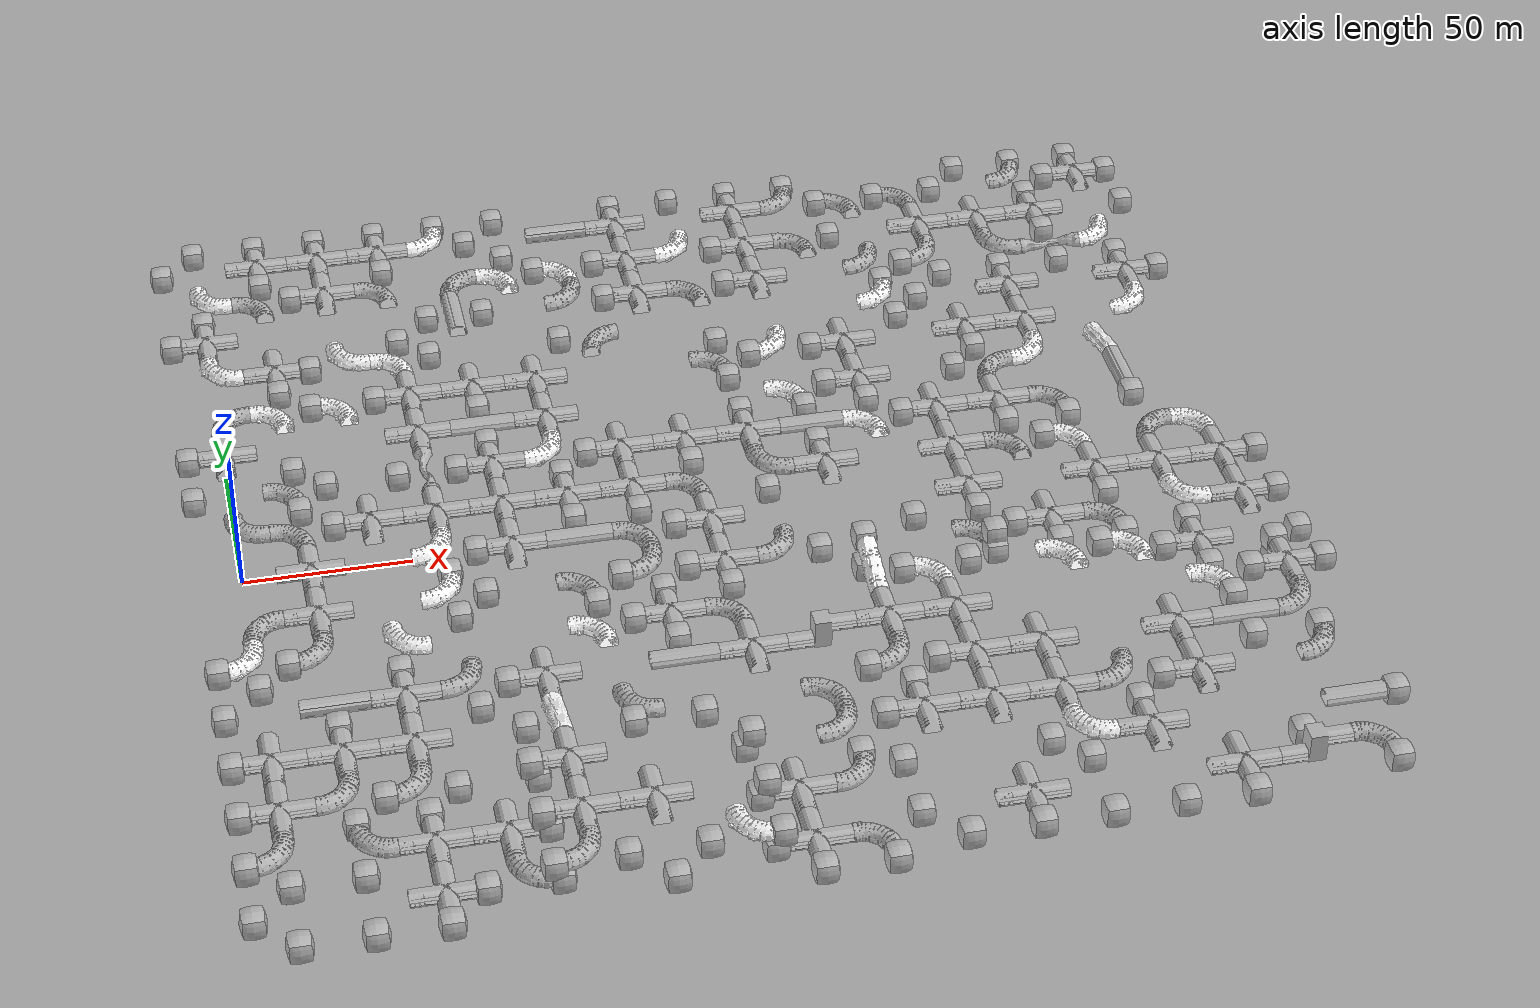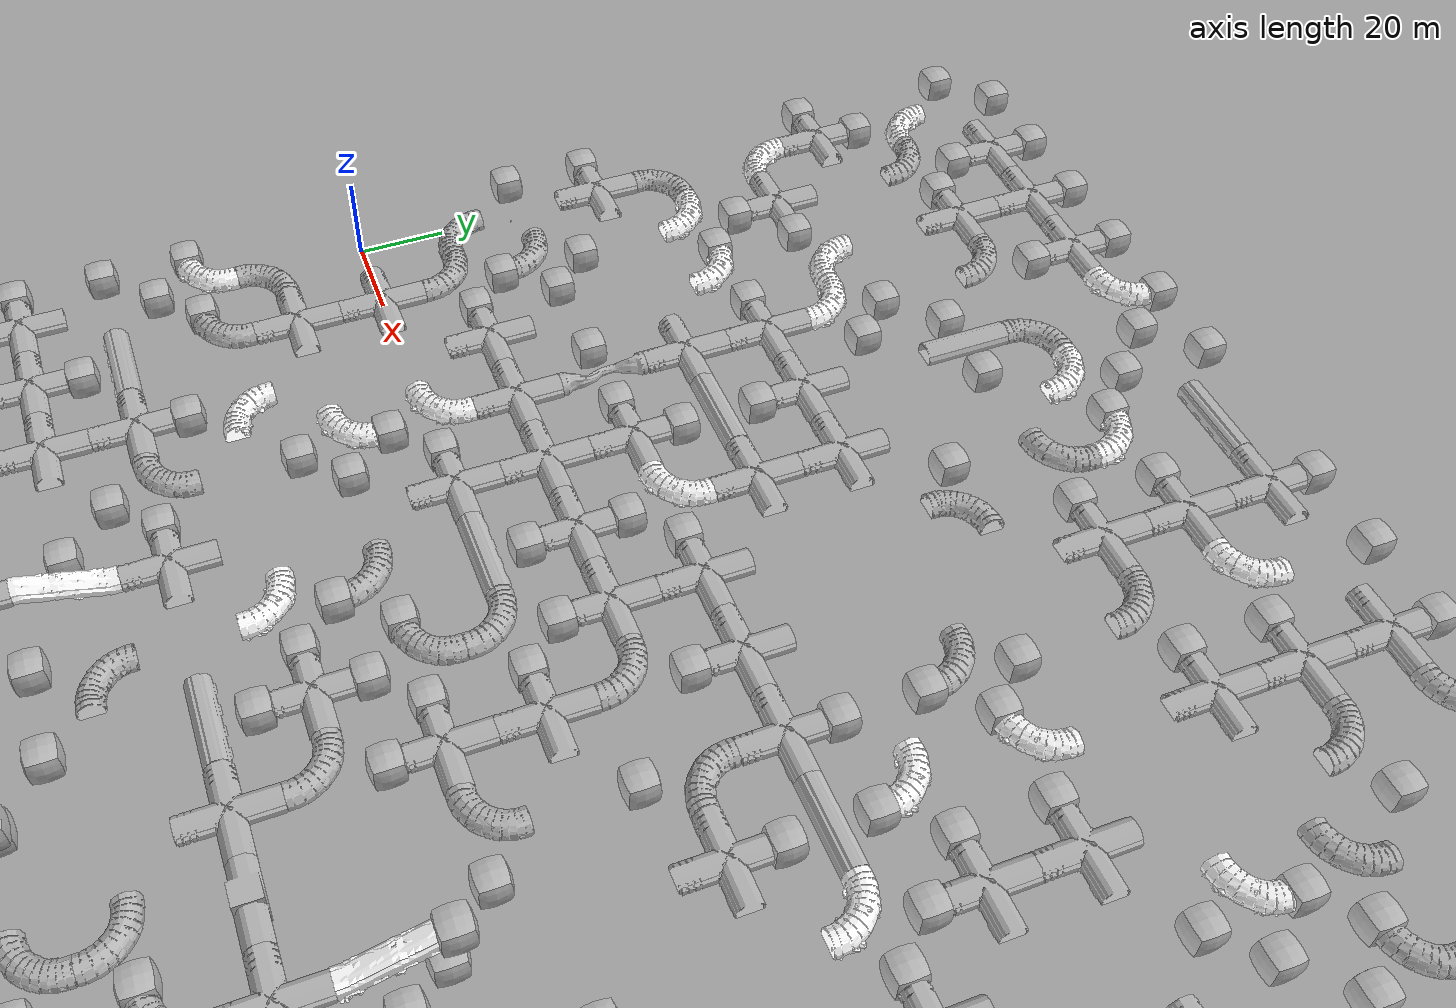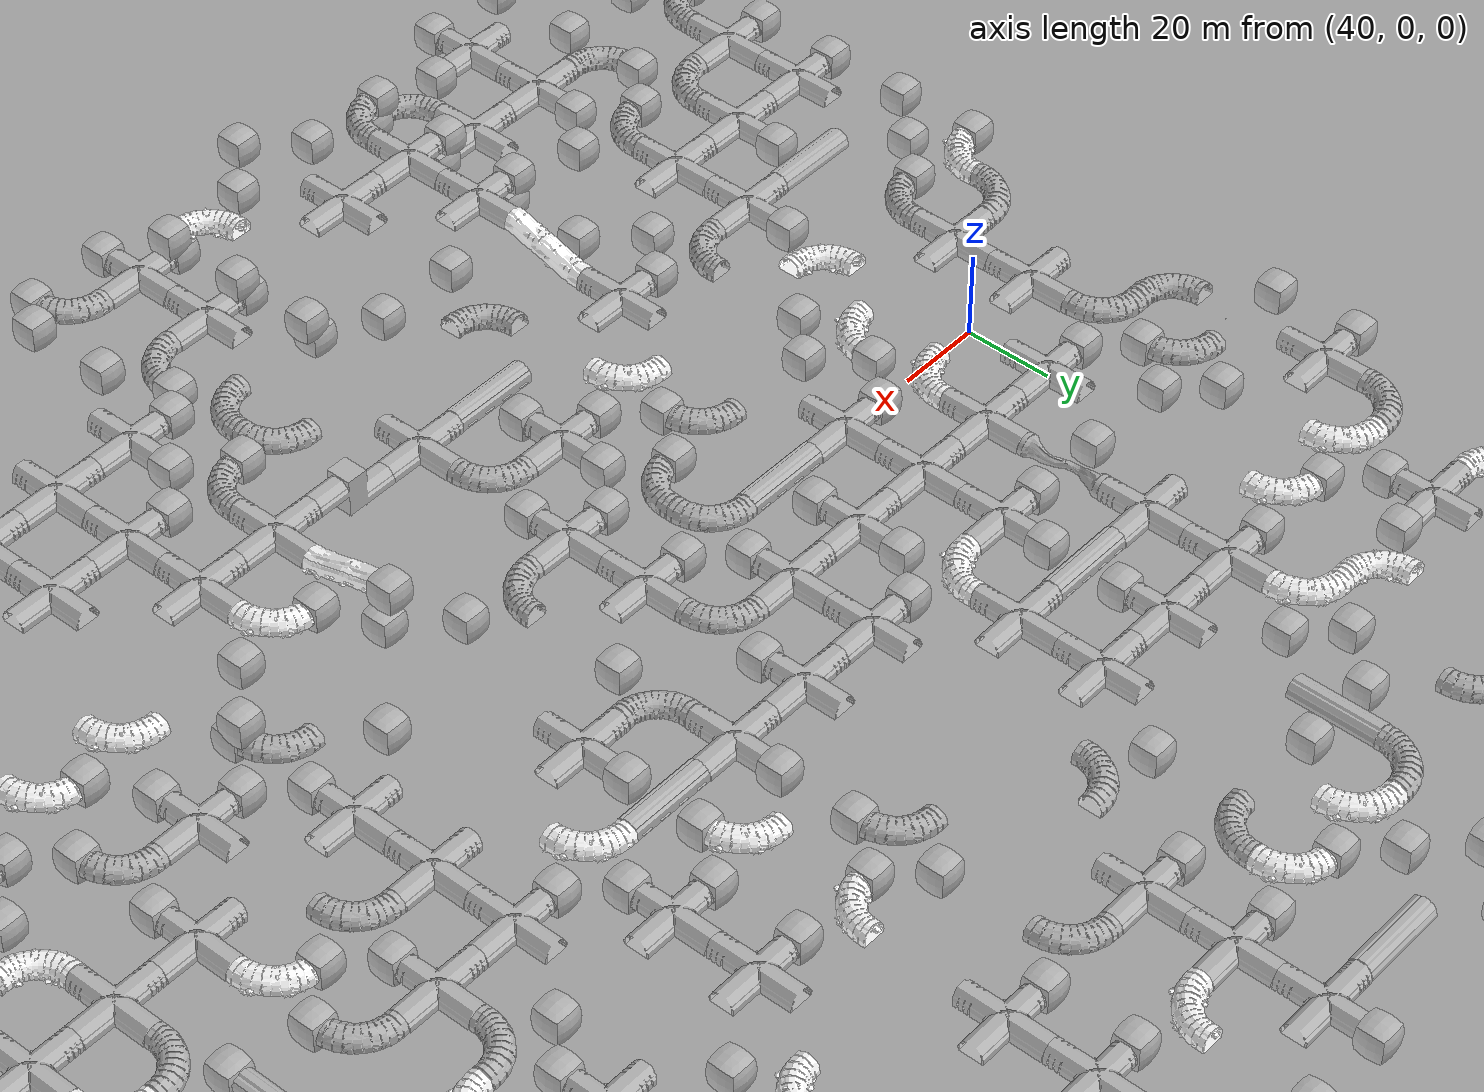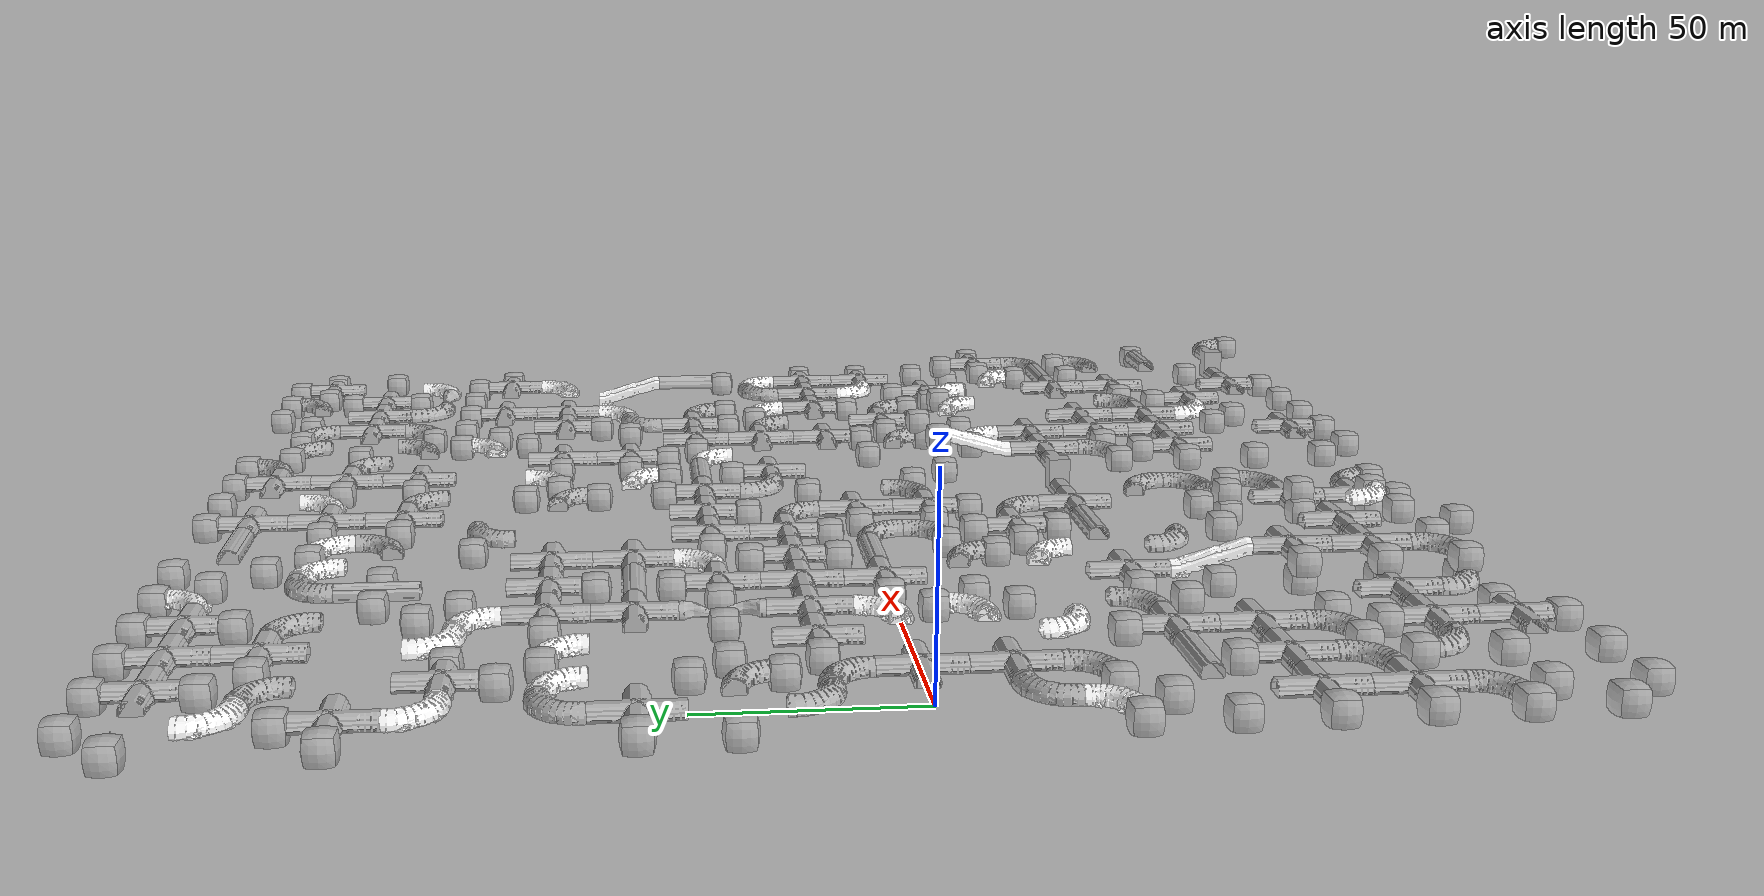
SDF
<sdf version="1.6">
 <world name="tunnel_circuit_practice_01">
  <scene>
   <ambient>0.2 0.2 0.2 1.0</ambient>
   <background>0.34 0.39 0.43 1.0</background>
   <grid>false</grid>
   <origin_visual>false</origin_visual>
  </scene>
  <include><name>artifact_origin</name><pose>10 0 0.0 0 0 0</pose><uri>model://fiducial</uri></include>
  <include>
   <name>tile_2</name>
   <uri>model://tunnel_tile_blocker</uri>
   <pose>-11.000000 160.000000 0.000000 0 0 0.000000</pose>
  </include>
  <include>
   <name>tile_3</name>
   <uri>model://tunnel_tile_blocker</uri>
   <pose>0.000000 171.000000 0.000000 0 0 0.000000</pose>
  </include>
  <include>
   <name>extinguisher_1</name>
   <uri>model://Extinguisher</uri>
   <pose>2.100000 162.100000 0.004000 0 0 0.000000</pose>
  </include>
  <include>
   <name>tile_4</name>
   <uri>model://tunnel_tile_1</uri>
   <pose>20.000000 160.000000 0.000000 0 0 0.000000</pose>
  </include>
  <include>
   <name>tile_5</name>
   <uri>model://tunnel_tile_blocker</uri>
   <pose>20.000000 149.000000 0.000000 0 0 0.000000</pose>
  </include>
  <include>
   <name>tile_6</name>
   <uri>model://tunnel_tile_blocker</uri>
   <pose>20.000000 171.000000 0.000000 0 0 0.000000</pose>
  </include>
  <include>
   <name>tile_7</name>
   <uri>model://tunnel_tile_1</uri>
   <pose>40.000000 160.000000 0.000000 0 0 0.000000</pose>
  </include>
  <include>
   <name>tile_8</name>
   <uri>model://tunnel_tile_blocker</uri>
   <pose>40.000000 171.000000 0.000000 0 0 0.000000</pose>
  </include>
  <include>
   <name>tile_9</name>
   <uri>model://tunnel_tile_1</uri>
   <pose>60.000000 160.000000 0.000000 0 0 0.000000</pose>
  </include>
  <include>
   <name>tile_10</name>
   <uri>model://tunnel_tile_blocker</uri>
   <pose>60.000000 171.000000 0.000000 0 0 0.000000</pose>
  </include>
  <include>
   <name>tile_11</name>
   <uri>model://tunnel_tile_blocker</uri>
   <pose>60.000000 149.000000 0.000000 0 0 0.000000</pose>
  </include>
  <include>
   <name>tile_12</name>
   <uri>model://Rough Tunnel Tile 90-degree Turn</uri>
   <pose>80.000000 160.000000 0.000000 0 0 3.141593</pose>
  </include>
  <include>
   <name>tile_13</name>
   <uri>model://tunnel_tile_blocker</uri>
   <pose>80.000000 171.000000 0.000000 0 0 0.000000</pose>
  </include>
  <include>
   <name>tile_15</name>
   <uri>model://tunnel_tile_blocker</uri>
   <pose>100.000000 149.000000 0.000000 0 0 0.000000</pose>
  </include>
  <include>
   <name>tile_16</name>
   <uri>model://tunnel_tile_blocker</uri>
   <pose>100.000000 171.000000 0.000000 0 0 0.000000</pose>
  </include>
  <include>
   <name>tile_17</name>
   <uri>model://tunnel_tile_blocker</uri>
   <pose>89.000000 160.000000 0.000000 0 0 0.000000</pose>
  </include>
  <include>
   <name>tile_18</name>
   <uri>model://tunnel_tile_5</uri>
   <pose>120.000000 160.000000 0.000000 0 0 4.712389</pose>
  </include>
  <include>
   <name>tile_19</name>
   <uri>model://tunnel_tile_1</uri>
   <pose>140.000000 160.000000 0.000000 0 0 0.000000</pose>
  </include>
  <include>
   <name>tile_20</name>
   <uri>model://tunnel_tile_blocker</uri>
   <pose>140.000000 171.000000 0.000000 0 0 0.000000</pose>
  </include>
  <include>
   <name>tile_22</name>
   <uri>model://tunnel_tile_blocker</uri>
   <pose>160.000000 171.000000 0.000000 0 0 0.000000</pose>
  </include>
  <include>
   <name>tile_23</name>
   <uri>model://tunnel_tile_1</uri>
   <pose>180.000000 160.000000 0.000000 0 0 0.000000</pose>
  </include>
  <include>
   <name>tile_24</name>
   <uri>model://tunnel_tile_blocker</uri>
   <pose>180.000000 171.000000 0.000000 0 0 0.000000</pose>
  </include>
  <include>
   <name>tile_25</name>
   <uri>model://tunnel_tile_2</uri>
   <pose>200.000000 160.000000 0.000000 0 0 3.141593</pose>
  </include>
  <include>
   <name>tile_26</name>
   <uri>model://tunnel_tile_blocker</uri>
   <pose>200.000000 171.000000 0.000000 0 0 0.000000</pose>
  </include>
  <include>
   <name>tile_27</name>
   <uri>model://tunnel_tile_2</uri>
   <pose>220.000000 160.000000 0.000000 0 0 4.712389</pose>
  </include>
  <include>
   <name>tile_28</name>
   <uri>model://tunnel_tile_blocker</uri>
   <pose>209.000000 160.000000 0.000000 0 0 0.000000</pose>
  </include>
  <include>
   <name>tile_29</name>
   <uri>model://tunnel_tile_2</uri>
   <pose>240.000000 160.000000 0.000000 0 0 4.712389</pose>
  </include>
  <include>
   <name>tile_30</name>
   <uri>model://tunnel_tile_blocker</uri>
   <pose>229.000000 160.000000 0.000000 0 0 0.000000</pose>
  </include>
  <include>
   <name>tile_32</name>
   <uri>model://tunnel_tile_blocker</uri>
   <pose>249.000000 160.000000 0.000000 0 0 0.000000</pose>
  </include>
  <include>
   <name>tile_33</name>
   <uri>model://tunnel_tile_blocker</uri>
   <pose>260.000000 171.000000 0.000000 0 0 0.000000</pose>
  </include>
  <include>
   <name>tile_34</name>
   <uri>model://tunnel_tile_2</uri>
   <pose>280.000000 160.000000 0.000000 0 0 3.141593</pose>
  </include>
  <include>
   <name>tile_35</name>
   <uri>model://tunnel_tile_blocker</uri>
   <pose>280.000000 171.000000 0.000000 0 0 0.000000</pose>
  </include>
  <include>
   <name>tile_36</name>
   <uri>model://tunnel_tile_1</uri>
   <pose>300.000000 160.000000 0.000000 0 0 0.000000</pose>
  </include>
  <include>
   <name>tile_37</name>
   <uri>model://tunnel_tile_blocker</uri>
   <pose>289.000000 160.000000 0.000000 0 0 0.000000</pose>
  </include>
  <include>
   <name>tile_38</name>
   <uri>model://tunnel_tile_blocker</uri>
   <pose>311.000000 160.000000 0.000000 0 0 0.000000</pose>
  </include>
  <include>
   <name>tile_39</name>
   <uri>model://tunnel_tile_blocker</uri>
   <pose>300.000000 171.000000 0.000000 0 0 0.000000</pose>
  </include>
  <include>
   <name>tile_40</name>
   <uri>model://Rough Tunnel Tile 90-degree Turn</uri>
   <pose>0.000000 140.000000 0.000000 0 0 1.570796</pose>
  </include>
  <include>
   <name>tile_41</name>
   <uri>model://tunnel_tile_2</uri>
   <pose>20.000000 140.000000 0.000000 0 0 4.712389</pose>
  </include>
  <include>
   <name>tile_42</name>
   <uri>model://tunnel_tile_1</uri>
   <pose>40.000000 140.000000 0.000000 0 0 0.000000</pose>
  </include>
  <include>
   <name>tile_43</name>
   <uri>model://tunnel_tile_blocker</uri>
   <pose>29.000000 140.000000 0.000000 0 0 0.000000</pose>
  </include>
  <include>
   <name>tile_44</name>
   <uri>model://tunnel_tile_2</uri>
   <pose>60.000000 140.000000 0.000000 0 0 4.712389</pose>
  </include>
  <include>
   <name>tile_45</name>
   <uri>model://tunnel_tile_2</uri>
   <pose>80.000000 140.000000 0.000000 0 0 0.000000</pose>
  </include>
  <include>
   <name>tile_46</name>
   <uri>model://Rough Tunnel Tile 90-degree Turn</uri>
   <pose>100.000000 140.000000 0.000000 0 0 4.712389</pose>
  </include>
  <include>
   <name>tile_47</name>
   <uri>model://Rough Tunnel Tile 90-degree Turn</uri>
   <pose>120.000000 140.000000 0.000000 0 0 4.712389</pose>
  </include>
  <include>
   <name>tile_48</name>
   <uri>model://tunnel_tile_blocker</uri>
   <pose>109.000000 140.000000 0.000000 0 0 0.000000</pose>
  </include>
  <include>
   <name>tile_49</name>
   <uri>model://tunnel_tile_1</uri>
   <pose>140.000000 140.000000 0.000000 0 0 0.000000</pose>
  </include>
  <include>
   <name>tile_50</name>
   <uri>model://tunnel_tile_blocker</uri>
   <pose>129.000000 140.000000 0.000000 0 0 0.000000</pose>
  </include>
  <include>
   <name>tile_51</name>
   <uri>model://Rough Tunnel Tile 90-degree Turn</uri>
   <pose>160.000000 140.000000 0.000000 0 0 3.141593</pose>
  </include>
  <include>
   <name>tile_52</name>
   <uri>model://tunnel_tile_1</uri>
   <pose>180.000000 140.000000 0.000000 0 0 0.000000</pose>
  </include>
  <include>
   <name>tile_53</name>
   <uri>model://tunnel_tile_blocker</uri>
   <pose>169.000000 140.000000 0.000000 0 0 0.000000</pose>
  </include>
  <include>
   <name>tile_54</name>
   <uri>model://tunnel_tile_2</uri>
   <pose>200.000000 140.000000 0.000000 0 0 4.712389</pose>
  </include>
  <include>
   <name>tile_56</name>
   <uri>model://tunnel_tile_blocker</uri>
   <pose>209.000000 140.000000 0.000000 0 0 0.000000</pose>
  </include>
  <include>
   <name>tile_57</name>
   <uri>model://tunnel_tile_1</uri>
   <pose>240.000000 140.000000 0.000000 0 0 0.000000</pose>
  </include>
  <include>
   <name>tile_58</name>
   <uri>model://tunnel_tile_1</uri>
   <pose>260.000000 140.000000 0.000000 0 0 0.000000</pose>
  </include>
  <include>
   <name>tile_59</name>
   <uri>model://tunnel_tile_1</uri>
   <pose>280.000000 140.000000 0.000000 0 0 0.000000</pose>
  </include>
  <include>
   <name>tile_60</name>
   <uri>model://tunnel_tile_blocker</uri>
   <pose>280.000000 151.000000 0.000000 0 0 0.000000</pose>
  </include>
  <include>
   <name>tile_61</name>
   <uri>model://tunnel_tile_blocker</uri>
   <pose>280.000000 129.000000 0.000000 0 0 0.000000</pose>
  </include>
  <include>
   <name>extinguisher_2</name>
   <uri>model://Extinguisher</uri>
   <pose>282.100000 137.900000 0.004000 0 0 1.570796</pose>
  </include>
  <include>
   <name>tile_63</name>
   <uri>model://tunnel_tile_blocker</uri>
   <pose>311.000000 140.000000 0.000000 0 0 0.000000</pose>
  </include>
  <include>
   <name>tile_64</name>
   <uri>model://tunnel_tile_1</uri>
   <pose>0.000000 120.000000 0.000000 0 0 0.000000</pose>
  </include>
  <include>
   <name>tile_65</name>
   <uri>model://tunnel_tile_blocker</uri>
   <pose>0.000000 131.000000 0.000000 0 0 0.000000</pose>
  </include>
  <include>
   <name>tile_66</name>
   <uri>model://tunnel_tile_blocker</uri>
   <pose>-11.000000 120.000000 0.000000 0 0 0.000000</pose>
  </include>
  <include>
   <name>tile_70</name>
   <uri>model://tunnel_tile_blocker</uri>
   <pose>60.000000 109.000000 0.000000 0 0 0.000000</pose>
  </include>
  <include>
   <name>tile_71</name>
   <uri>model://tunnel_tile_blocker</uri>
   <pose>71.000000 120.000000 0.000000 0 0 0.000000</pose>
  </include>
  <include>
   <name>tile_72</name>
   <uri>model://tunnel_tile_5</uri>
   <pose>80.000000 120.000000 0.000000 0 0 3.141593</pose>
  </include>
  <include>
   <name>tile_74</name>
   <uri>model://tunnel_tile_blocker</uri>
   <pose>89.000000 120.000000 0.000000 0 0 0.000000</pose>
  </include>
  <include>
   <name>tile_75</name>
   <uri>model://tunnel_tile_2</uri>
   <pose>120.000000 120.000000 0.000000 0 0 3.141593</pose>
  </include>
  <include>
   <name>tile_76</name>
   <uri>model://tunnel_tile_1</uri>
   <pose>140.000000 120.000000 0.000000 0 0 0.000000</pose>
  </include>
  <include>
   <name>tile_77</name>
   <uri>model://tunnel_tile_blocker</uri>
   <pose>129.000000 120.000000 0.000000 0 0 0.000000</pose>
  </include>
  <include>
   <name>tile_78</name>
   <uri>model://tunnel_tile_2</uri>
   <pose>160.000000 120.000000 0.000000 0 0 4.712389</pose>
  </include>
  <include>
   <name>tile_79</name>
   <uri>model://tunnel_tile_1</uri>
   <pose>180.000000 120.000000 0.000000 0 0 0.000000</pose>
  </include>
  <include>
   <name>tile_80</name>
   <uri>model://tunnel_tile_blocker</uri>
   <pose>169.000000 120.000000 0.000000 0 0 0.000000</pose>
  </include>
  <include>
   <name>tile_82</name>
   <uri>model://tunnel_tile_2</uri>
   <pose>220.000000 120.000000 0.000000 0 0 3.141593</pose>
  </include>
  <include>
   <name>tile_83</name>
   <uri>model://tunnel_tile_2</uri>
   <pose>240.000000 120.000000 0.000000 0 0 3.141593</pose>
  </include>
  <include>
   <name>tile_84</name>
   <uri>model://tunnel_tile_blocker</uri>
   <pose>229.000000 120.000000 0.000000 0 0 0.000000</pose>
  </include>
  <include>
   <name>tile_85</name>
   <uri>model://tunnel_tile_2</uri>
   <pose>260.000000 120.000000 0.000000 0 0 1.570796</pose>
  </include>
  <include>
   <name>tile_86</name>
   <uri>model://constrained_tunnel_tile_short</uri>
   <pose>280.000000 120.000000 0.000000 0 0 1.570796</pose>
  </include>
  <include>
   <name>tile_87</name>
   <uri>model://Rough Tunnel Tile 90-degree Turn</uri>
   <pose>300.000000 120.000000 0.000000 0 0 3.141593</pose>
  </include>
  <include>
   <name>tile_88</name>
   <uri>model://Rough Tunnel Tile 90-degree Turn</uri>
   <pose>0.000000 100.000000 0.000000 0 0 1.570796</pose>
  </include>
  <include>
   <name>tile_89</name>
   <uri>model://tunnel_tile_1</uri>
   <pose>20.000000 100.000000 0.000000 0 0 0.000000</pose>
  </include>
  <include>
   <name>tile_90</name>
   <uri>model://tunnel_tile_blocker</uri>
   <pose>31.000000 100.000000 0.000000 0 0 0.000000</pose>
  </include>
  <include>
   <name>tile_91</name>
   <uri>model://tunnel_tile_blocker</uri>
   <pose>20.000000 89.000000 0.000000 0 0 0.000000</pose>
  </include>
  <include>
   <name>tile_92</name>
   <uri>model://Rough Tunnel Tile 90-degree Turn</uri>
   <pose>40.000000 100.000000 0.000000 0 0 1.570796</pose>
  </include>
  <include>
   <name>tile_93</name>
   <uri>model://Rough Tunnel Tile 90-degree Turn</uri>
   <pose>60.000000 100.000000 0.000000 0 0 4.712389</pose>
  </include>
  <include>
   <name>tile_95</name>
   <uri>model://tunnel_tile_blocker</uri>
   <pose>69.000000 100.000000 0.000000 0 0 0.000000</pose>
  </include>
  <include>
   <name>tile_97</name>
   <uri>model://tunnel_tile_blocker</uri>
   <pose>111.000000 100.000000 0.000000 0 0 0.000000</pose>
  </include>
  <include>
   <name>tile_98</name>
   <uri>model://tunnel_tile_2</uri>
   <pose>120.000000 100.000000 0.000000 0 0 0.000000</pose>
  </include>
  <include>
   <name>tile_101</name>
   <uri>model://tunnel_tile_blocker</uri>
   <pose>160.000000 89.000000 0.000000 0 0 0.000000</pose>
  </include>
  <include>
   <name>tile_104</name>
   <uri>model://Rough Tunnel Tile 90-degree Turn</uri>
   <pose>220.000000 100.000000 0.000000 0 0 3.141593</pose>
  </include>
  <include>
   <name>tile_105</name>
   <uri>model://tunnel_tile_blocker</uri>
   <pose>220.000000 111.000000 0.000000 0 0 0.000000</pose>
  </include>
  <include>
   <name>tile_107</name>
   <uri>model://tunnel_tile_blocker</uri>
   <pose>229.000000 100.000000 0.000000 0 0 0.000000</pose>
  </include>
  <include>
   <name>tile_108</name>
   <uri>model://tunnel_tile_blocker</uri>
   <pose>240.000000 111.000000 0.000000 0 0 0.000000</pose>
  </include>
  <include>
   <name>tile_109</name>
   <uri>model://tunnel_tile_1</uri>
   <pose>260.000000 100.000000 0.000000 0 0 0.000000</pose>
  </include>
  <include>
   <name>tile_110</name>
   <uri>model://tunnel_tile_blocker</uri>
   <pose>260.000000 111.000000 0.000000 0 0 0.000000</pose>
  </include>
  <include>
   <name>tile_112</name>
   <uri>model://tunnel_tile_blocker</uri>
   <pose>280.000000 111.000000 0.000000 0 0 0.000000</pose>
  </include>
  <include>
   <name>tile_113</name>
   <uri>model://tunnel_tile_1</uri>
   <pose>300.000000 100.000000 0.000000 0 0 0.000000</pose>
  </include>
  <include>
   <name>tile_114</name>
   <uri>model://tunnel_tile_blocker</uri>
   <pose>300.000000 111.000000 0.000000 0 0 0.000000</pose>
  </include>
  <include>
   <name>tile_115</name>
   <uri>model://tunnel_tile_blocker</uri>
   <pose>311.000000 100.000000 0.000000 0 0 0.000000</pose>
  </include>
  <include>
   <name>tile_116</name>
   <uri>model://tunnel_tile_2</uri>
   <pose>0.000000 80.000000 0.000000 0 0 0.000000</pose>
  </include>
  <include>
   <name>tile_117</name>
   <uri>model://Rough Tunnel Tile 90-degree Turn</uri>
   <pose>20.000000 80.000000 0.000000 0 0 4.712389</pose>
  </include>
  <include>
   <name>tile_118</name>
   <uri>model://Rough Tunnel Tile 90-degree Turn</uri>
   <pose>40.000000 80.000000 0.000000 0 0 4.712389</pose>
  </include>
  <include>
   <name>tile_119</name>
   <uri>model://tunnel_tile_blocker</uri>
   <pose>29.000000 80.000000 0.000000 0 0 0.000000</pose>
  </include>
  <include>
   <name>phone_1</name>
   <uri>model://Phone</uri>
   <pose>34.000000 80.000000 0.004000 -1.570796 0 -0.523599</pose>
  </include>
  <include>
   <name>tile_120</name>
   <uri>model://tunnel_tile_1</uri>
   <pose>60.000000 80.000000 0.000000 0 0 0.000000</pose>
  </include>
  <include>
   <name>tile_121</name>
   <uri>model://tunnel_tile_blocker</uri>
   <pose>49.000000 80.000000 0.000000 0 0 0.000000</pose>
  </include>
  <include>
   <name>tile_122</name>
   <uri>model://tunnel_tile_1</uri>
   <pose>80.000000 80.000000 0.000000 0 0 0.000000</pose>
  </include>
  <include>
   <name>tile_123</name>
   <uri>model://tunnel_tile_blocker</uri>
   <pose>80.000000 69.000000 0.000000 0 0 0.000000</pose>
  </include>
  <include>
   <name>tile_124</name>
   <uri>model://tunnel_tile_1</uri>
   <pose>100.000000 80.000000 0.000000 0 0 0.000000</pose>
  </include>
  <include>
   <name>tile_127</name>
   <uri>model://tunnel_tile_2</uri>
   <pose>160.000000 80.000000 0.000000 0 0 4.712389</pose>
  </include>
  <include>
   <name>tile_128</name>
   <uri>model://tunnel_tile_blocker</uri>
   <pose>160.000000 69.000000 0.000000 0 0 0.000000</pose>
  </include>
  <include>
   <name>tile_129</name>
   <uri>model://Rough Tunnel Tile 90-degree Turn</uri>
   <pose>180.000000 80.000000 0.000000 0 0 3.141593</pose>
  </include>
  <include>
   <name>tile_130</name>
   <uri>model://tunnel_tile_blocker</uri>
   <pose>169.000000 80.000000 0.000000 0 0 0.000000</pose>
  </include>
  <include>
   <name>tile_131</name>
   <uri>model://tunnel_tile_1</uri>
   <pose>200.000000 80.000000 0.000000 0 0 0.000000</pose>
  </include>
  <include>
   <name>tile_132</name>
   <uri>model://tunnel_tile_blocker</uri>
   <pose>189.000000 80.000000 0.000000 0 0 0.000000</pose>
  </include>
  <include>
   <name>tile_134</name>
   <uri>model://tunnel_tile_blocker</uri>
   <pose>220.000000 91.000000 0.000000 0 0 0.000000</pose>
  </include>
  <include>
   <name>tile_135</name>
   <uri>model://tunnel_tile_1</uri>
   <pose>240.000000 80.000000 0.000000 0 0 0.000000</pose>
  </include>
  <include>
   <name>tile_136</name>
   <uri>model://tunnel_tile_blocker</uri>
   <pose>240.000000 69.000000 0.000000 0 0 0.000000</pose>
  </include>
  <include>
   <name>tile_137</name>
   <uri>model://tunnel_tile_1</uri>
   <pose>260.000000 80.000000 0.000000 0 0 0.000000</pose>
  </include>
  <include>
   <name>tile_139</name>
   <uri>model://Rough Tunnel Tile 90-degree Turn</uri>
   <pose>300.000000 80.000000 0.000000 0 0 3.141593</pose>
  </include>
  <include>
   <name>tile_140</name>
   <uri>model://tunnel_tile_1</uri>
   <pose>0.000000 60.000000 0.000000 0 0 0.000000</pose>
  </include>
  <include>
   <name>tile_141</name>
   <uri>model://tunnel_tile_blocker</uri>
   <pose>-11.000000 60.000000 0.000000 0 0 0.000000</pose>
  </include>
  <include>
   <name>tile_143</name>
   <uri>model://tunnel_tile_blocker</uri>
   <pose>20.000000 49.000000 0.000000 0 0 0.000000</pose>
  </include>
  <include>
   <name>tile_145</name>
   <uri>model://tunnel_tile_1</uri>
   <pose>60.000000 60.000000 0.000000 0 0 0.000000</pose>
  </include>
  <include>
   <name>tile_146</name>
   <uri>model://tunnel_tile_5</uri>
   <pose>80.000000 60.000000 0.000000 0 0 1.570796</pose>
  </include>
  <include>
   <name>tile_147</name>
   <uri>model://tunnel_tile_1</uri>
   <pose>100.000000 60.000000 0.000000 0 0 0.000000</pose>
  </include>
  <include>
   <name>tile_151</name>
   <uri>model://Rough Tunnel Tile 90-degree Turn</uri>
   <pose>180.000000 60.000000 0.000000 0 0 4.712389</pose>
  </include>
  <include>
   <name>tile_152</name>
   <uri>model://tunnel_tile_blocker</uri>
   <pose>180.000000 49.000000 0.000000 0 0 0.000000</pose>
  </include>
  <include>
   <name>tile_153</name>
   <uri>model://tunnel_tile_1</uri>
   <pose>200.000000 60.000000 0.000000 0 0 0.000000</pose>
  </include>
  <include>
   <name>tile_154</name>
   <uri>model://tunnel_tile_blocker</uri>
   <pose>189.000000 60.000000 0.000000 0 0 0.000000</pose>
  </include>
  <include>
   <name>tile_155</name>
   <uri>model://tunnel_tile_blocker</uri>
   <pose>200.000000 49.000000 0.000000 0 0 0.000000</pose>
  </include>
  <include>
   <name>tile_157</name>
   <uri>model://tunnel_tile_blocker</uri>
   <pose>231.000000 60.000000 0.000000 0 0 0.000000</pose>
  </include>
  <include>
   <name>tile_158</name>
   <uri>model://tunnel_tile_2</uri>
   <pose>240.000000 60.000000 0.000000 0 0 0.000000</pose>
  </include>
  <include>
   <name>tile_159</name>
   <uri>model://Rough Tunnel Tile 90-degree Turn</uri>
   <pose>260.000000 60.000000 0.000000 0 0 3.141593</pose>
  </include>
  <include>
   <name>tile_160</name>
   <uri>model://Rough Tunnel Tile Ramp</uri>
   <pose>280.000000 60.000000 0.000000 0 0 3.141593</pose>
  </include>
  <include>
   <name>tile_162</name>
   <uri>model://tunnel_tile_blocker</uri>
   <pose>-11.000000 40.000000 0.000000 0 0 0.000000</pose>
  </include>
  <include>
   <name>extinguisher_3</name>
   <uri>model://Extinguisher</uri>
   <pose>2.100000 37.000000 0.004000 0 0 0.000000</pose>
  </include>
  <include>
   <name>tile_163</name>
   <uri>model://tunnel_tile_2</uri>
   <pose>20.000000 40.000000 0.000000 0 0 4.712389</pose>
  </include>
  <include>
   <name>tile_164</name>
   <uri>model://tunnel_tile_blocker</uri>
   <pose>20.000000 29.000000 0.000000 0 0 0.000000</pose>
  </include>
  <include>
   <name>tile_166</name>
   <uri>model://tunnel_tile_blocker</uri>
   <pose>29.000000 40.000000 0.000000 0 0 0.000000</pose>
  </include>
  <include>
   <name>tile_167</name>
   <uri>model://tunnel_tile_blocker</uri>
   <pose>51.000000 40.000000 0.000000 0 0 0.000000</pose>
  </include>
  <include>
   <name>tile_168</name>
   <uri>model://constrained_tunnel_tile_short</uri>
   <pose>60.000000 40.000000 0.000000 0 0 3.141593</pose>
  </include>
  <include>
   <name>tile_169</name>
   <uri>model://tunnel_tile_1</uri>
   <pose>80.000000 40.000000 0.000000 0 0 0.000000</pose>
  </include>
  <include>
   <name>tile_170</name>
   <uri>model://tunnel_tile_blocker</uri>
   <pose>69.000000 40.000000 0.000000 0 0 0.000000</pose>
  </include>
  <include>
   <name>tile_171</name>
   <uri>model://tunnel_tile_blocker</uri>
   <pose>80.000000 51.000000 0.000000 0 0 0.000000</pose>
  </include>
  <include>
   <name>tile_172</name>
   <uri>model://Rough Tunnel Tile 90-degree Turn</uri>
   <pose>100.000000 40.000000 0.000000 0 0 3.141593</pose>
  </include>
  <include>
   <name>tile_173</name>
   <uri>model://tunnel_tile_1</uri>
   <pose>120.000000 40.000000 0.000000 0 0 0.000000</pose>
  </include>
  <include>
   <name>tile_174</name>
   <uri>model://tunnel_tile_blocker</uri>
   <pose>109.000000 40.000000 0.000000 0 0 0.000000</pose>
  </include>
  <include>
   <name>tile_175</name>
   <uri>model://tunnel_tile_1</uri>
   <pose>140.000000 40.000000 0.000000 0 0 0.000000</pose>
  </include>
  <include>
   <name>tile_176</name>
   <uri>model://tunnel_tile_blocker</uri>
   <pose>140.000000 29.000000 0.000000 0 0 0.000000</pose>
  </include>
  <include>
   <name>tile_177</name>
   <uri>model://tunnel_tile_1</uri>
   <pose>160.000000 40.000000 0.000000 0 0 0.000000</pose>
  </include>
  <include>
   <name>tile_178</name>
   <uri>model://tunnel_tile_blocker</uri>
   <pose>160.000000 51.000000 0.000000 0 0 0.000000</pose>
  </include>
  <include>
   <name>tile_179</name>
   <uri>model://tunnel_tile_5</uri>
   <pose>180.000000 40.000000 0.000000 0 0 1.570796</pose>
  </include>
  <include>
   <name>tile_180</name>
   <uri>model://Rough Tunnel Tile 90-degree Turn</uri>
   <pose>200.000000 40.000000 0.000000 0 0 4.712389</pose>
  </include>
  <include>
   <name>tile_181</name>
   <uri>model://tunnel_tile_1</uri>
   <pose>220.000000 40.000000 0.000000 0 0 0.000000</pose>
  </include>
  <include>
   <name>tile_182</name>
   <uri>model://tunnel_tile_blocker</uri>
   <pose>209.000000 40.000000 0.000000 0 0 0.000000</pose>
  </include>
  <include>
   <name>tile_183</name>
   <uri>model://tunnel_tile_1</uri>
   <pose>240.000000 40.000000 0.000000 0 0 0.000000</pose>
  </include>
  <include>
   <name>tile_184</name>
   <uri>model://tunnel_tile_blocker</uri>
   <pose>240.000000 29.000000 0.000000 0 0 0.000000</pose>
  </include>
  <include>
   <name>tile_185</name>
   <uri>model://tunnel_tile_2</uri>
   <pose>260.000000 40.000000 0.000000 0 0 4.712389</pose>
  </include>
  <include>
   <name>tile_186</name>
   <uri>model://tunnel_tile_blocker</uri>
   <pose>260.000000 29.000000 0.000000 0 0 0.000000</pose>
  </include>
  <include>
   <name>tile_187</name>
   <uri>model://tunnel_tile_5</uri>
   <pose>280.000000 40.000000 5.000000 0 0 0.000000</pose>
  </include>
  <include>
   <name>tile_188</name>
   <uri>model://tunnel_tile_blocker</uri>
   <pose>280.000000 29.000000 5.000000 0 0 0.000000</pose>
  </include>
  <include>
   <name>phone_2</name>
   <uri>model://Phone</uri>
   <pose>277.900000 43.000000 5.004000 -1.570796 0 0.000000</pose>
  </include>
  <include>
   <name>tile_189</name>
   <uri>model://tunnel_tile_2</uri>
   <pose>0.000000 20.000000 0.000000 0 0 1.570796</pose>
  </include>
  <include>
   <name>tile_190</name>
   <uri>model://tunnel_tile_2</uri>
   <pose>20.000000 20.000000 0.000000 0 0 4.712389</pose>
  </include>
  <include>
   <name>tile_191</name>
   <uri>model://tunnel_tile_1</uri>
   <pose>40.000000 20.000000 0.000000 0 0 0.000000</pose>
  </include>
  <include>
   <name>tile_192</name>
   <uri>model://tunnel_tile_blocker</uri>
   <pose>29.000000 20.000000 0.000000 0 0 0.000000</pose>
  </include>
  <include>
   <name>backpack_1</name>
   <uri>model://Backpack</uri>
   <pose>41.000000 14.000000 0.004000 0 0 0.000000</pose>
  </include>
  <include>
   <name>tile_193</name>
   <uri>model://tunnel_tile_1</uri>
   <pose>60.000000 20.000000 0.000000 0 0 0.000000</pose>
  </include>
  <include>
   <name>tile_194</name>
   <uri>model://tunnel_tile_1</uri>
   <pose>80.000000 20.000000 0.000000 0 0 0.000000</pose>
  </include>
  <include>
   <name>tile_195</name>
   <uri>model://tunnel_tile_1</uri>
   <pose>100.000000 20.000000 0.000000 0 0 0.000000</pose>
  </include>
  <include>
   <name>tile_196</name>
   <uri>model://tunnel_tile_blocker</uri>
   <pose>100.000000 31.000000 0.000000 0 0 0.000000</pose>
  </include>
  <include>
   <name>tile_197</name>
   <uri>model://tunnel_tile_blocker</uri>
   <pose>100.000000 9.000000 0.000000 0 0 0.000000</pose>
  </include>
  <include>
   <name>tile_198</name>
   <uri>model://tunnel_tile_1</uri>
   <pose>120.000000 20.000000 0.000000 0 0 0.000000</pose>
  </include>
  <include>
   <name>tile_199</name>
   <uri>model://tunnel_tile_blocker</uri>
   <pose>120.000000 9.000000 0.000000 0 0 0.000000</pose>
  </include>
  <include>
   <name>tile_200</name>
   <uri>model://tunnel_tile_2</uri>
   <pose>140.000000 20.000000 0.000000 0 0 4.712389</pose>
  </include>
  <include>
   <name>tile_201</name>
   <uri>model://tunnel_tile_2</uri>
   <pose>160.000000 20.000000 0.000000 0 0 1.570796</pose>
  </include>
  <include>
   <name>tile_202</name>
   <uri>model://tunnel_tile_1</uri>
   <pose>180.000000 20.000000 0.000000 0 0 0.000000</pose>
  </include>
  <include>
   <name>tile_203</name>
   <uri>model://tunnel_tile_blocker</uri>
   <pose>180.000000 31.000000 0.000000 0 0 0.000000</pose>
  </include>
  <include>
   <name>tile_205</name>
   <uri>model://tunnel_tile_1</uri>
   <pose>220.000000 20.000000 0.000000 0 0 0.000000</pose>
  </include>
  <include>
   <name>tile_206</name>
   <uri>model://tunnel_tile_2</uri>
   <pose>240.000000 20.000000 0.000000 0 0 4.712389</pose>
  </include>
  <include>
   <name>tile_207</name>
   <uri>model://Rough Tunnel Tile 90-degree Turn</uri>
   <pose>260.000000 20.000000 0.000000 0 0 4.712389</pose>
  </include>
  <include>
   <name>tile_208</name>
   <uri>model://tunnel_tile_blocker</uri>
   <pose>249.000000 20.000000 0.000000 0 0 0.000000</pose>
  </include>
  <include>
   <name>tile_209</name>
   <uri>model://tunnel_tile_2</uri>
   <pose>280.000000 20.000000 0.000000 0 0 0.000000</pose>
  </include>
  <include>
   <name>tile_210</name>
   <uri>model://Rough Tunnel Tile 90-degree Turn</uri>
   <pose>300.000000 20.000000 0.000000 0 0 4.712389</pose>
  </include>
  <include>
   <name>tile_211</name>
   <uri>model://tunnel_tile_1</uri>
   <pose>20.000000 0.000000 0.000000 0 0 0.000000</pose>
  </include>
  <include>
   <name>tile_213</name>
   <uri>model://Rough Tunnel Tile 90-degree Turn</uri>
   <pose>60.000000 0.000000 0.000000 0 0 3.141593</pose>
  </include>
  <include>
   <name>tile_214</name>
   <uri>model://tunnel_tile_1</uri>
   <pose>80.000000 0.000000 0.000000 0 0 0.000000</pose>
  </include>
  <include>
   <name>tile_215</name>
   <uri>model://tunnel_tile_blocker</uri>
   <pose>69.000000 0.000000 0.000000 0 0 0.000000</pose>
  </include>
  <include>
   <name>tile_216</name>
   <uri>model://tunnel_tile_5</uri>
   <pose>100.000000 0.000000 0.000000 0 0 1.570796</pose>
  </include>
  <include>
   <name>tile_217</name>
   <uri>model://tunnel_tile_2</uri>
   <pose>120.000000 0.000000 0.000000 0 0 4.712389</pose>
  </include>
  <include>
   <name>tile_218</name>
   <uri>model://tunnel_tile_1</uri>
   <pose>140.000000 0.000000 0.000000 0 0 0.000000</pose>
  </include>
  <include>
   <name>tile_219</name>
   <uri>model://tunnel_tile_blocker</uri>
   <pose>129.000000 0.000000 0.000000 0 0 0.000000</pose>
  </include>
  <include>
   <name>tile_221</name>
   <uri>model://tunnel_tile_blocker</uri>
   <pose>160.000000 11.000000 0.000000 0 0 0.000000</pose>
  </include>
  <include>
   <name>tile_224</name>
   <uri>model://tunnel_tile_blocker</uri>
   <pose>200.000000 -11.000000 0.000000 0 0 0.000000</pose>
  </include>
  <include>
   <name>tile_225</name>
   <uri>model://tunnel_tile_1</uri>
   <pose>220.000000 0.000000 0.000000 0 0 0.000000</pose>
  </include>
  <include>
   <name>tile_226</name>
   <uri>model://tunnel_tile_blocker</uri>
   <pose>220.000000 -11.000000 0.000000 0 0 0.000000</pose>
  </include>
  <include>
   <name>tile_228</name>
   <uri>model://tunnel_tile_1</uri>
   <pose>260.000000 0.000000 0.000000 0 0 0.000000</pose>
  </include>
  <include>
   <name>tile_229</name>
   <uri>model://tunnel_tile_blocker</uri>
   <pose>260.000000 -11.000000 0.000000 0 0 0.000000</pose>
  </include>
  <include>
   <name>tile_230</name>
   <uri>model://tunnel_tile_1</uri>
   <pose>280.000000 0.000000 0.000000 0 0 0.000000</pose>
  </include>
  <include>
   <name>tile_231</name>
   <uri>model://tunnel_tile_1</uri>
   <pose>300.000000 0.000000 0.000000 0 0 0.000000</pose>
  </include>
  <include>
   <name>tile_232</name>
   <uri>model://tunnel_tile_blocker</uri>
   <pose>311.000000 0.000000 0.000000 0 0 0.000000</pose>
  </include>
  <include>
   <name>tile_233</name>
   <uri>model://tunnel_tile_2</uri>
   <pose>0.000000 -20.000000 0.000000 0 0 0.000000</pose>
  </include>
  <include>
   <name>tile_234</name>
   <uri>model://tunnel_tile_1</uri>
   <pose>20.000000 -20.000000 0.000000 0 0 0.000000</pose>
  </include>
  <include>
   <name>tile_236</name>
   <uri>model://Rough Tunnel Tile 90-degree Turn</uri>
   <pose>60.000000 -20.000000 0.000000 0 0 3.141593</pose>
  </include>
  <include>
   <name>tile_237</name>
   <uri>model://tunnel_tile_blocker</uri>
   <pose>60.000000 -9.000000 0.000000 0 0 0.000000</pose>
  </include>
  <include>
   <name>tile_239</name>
   <uri>model://tunnel_tile_blocker</uri>
   <pose>69.000000 -20.000000 0.000000 0 0 0.000000</pose>
  </include>
  <include>
   <name>tile_240</name>
   <uri>model://tunnel_tile_2</uri>
   <pose>100.000000 -20.000000 0.000000 0 0 4.712389</pose>
  </include>
  <include>
   <name>tile_241</name>
   <uri>model://tunnel_tile_blocker</uri>
   <pose>100.000000 -31.000000 0.000000 0 0 0.000000</pose>
  </include>
  <include>
   <name>tile_242</name>
   <uri>model://tunnel_tile_2</uri>
   <pose>120.000000 -20.000000 0.000000 0 0 3.141593</pose>
  </include>
  <include>
   <name>tile_243</name>
   <uri>model://tunnel_tile_blocker</uri>
   <pose>109.000000 -20.000000 0.000000 0 0 0.000000</pose>
  </include>
  <include>
   <name>phone_3</name>
   <uri>model://Phone</uri>
   <pose>117.000000 -20.200000 0.004000 -1.570796 0 0.000000</pose>
  </include>
  <include>
   <name>tile_244</name>
   <uri>model://tunnel_tile_1</uri>
   <pose>140.000000 -20.000000 0.000000 0 0 0.000000</pose>
  </include>
  <include>
   <name>tile_245</name>
   <uri>model://tunnel_tile_blocker</uri>
   <pose>129.000000 -20.000000 0.000000 0 0 0.000000</pose>
  </include>
  <include>
   <name>tile_246</name>
   <uri>model://tunnel_tile_blocker</uri>
   <pose>140.000000 -31.000000 0.000000 0 0 0.000000</pose>
  </include>
  <include>
   <name>phone_4</name>
   <uri>model://Phone</uri>
   <pose>137.000000 -17.900000 0.004000 -1.570796 0 -1.570796</pose>
  </include>
  <include>
   <name>tile_247</name>
   <uri>model://tunnel_tile_2</uri>
   <pose>160.000000 -20.000000 0.000000 0 0 3.141593</pose>
  </include>
  <include>
   <name>tile_249</name>
   <uri>model://tunnel_tile_blocker</uri>
   <pose>169.000000 -20.000000 0.000000 0 0 0.000000</pose>
  </include>
  <include>
   <name>tile_250</name>
   <uri>model://tunnel_tile_blocker</uri>
   <pose>180.000000 -31.000000 0.000000 0 0 0.000000</pose>
  </include>
  <include>
   <name>tile_252</name>
   <uri>model://tunnel_tile_2</uri>
   <pose>220.000000 -20.000000 0.000000 0 0 4.712389</pose>
  </include>
  <include>
   <name>tile_253</name>
   <uri>model://tunnel_tile_blocker</uri>
   <pose>220.000000 -31.000000 0.000000 0 0 0.000000</pose>
  </include>
  <include>
   <name>tile_254</name>
   <uri>model://tunnel_tile_1</uri>
   <pose>240.000000 -20.000000 0.000000 0 0 0.000000</pose>
  </include>
  <include>
   <name>tile_255</name>
   <uri>model://tunnel_tile_blocker</uri>
   <pose>229.000000 -20.000000 0.000000 0 0 0.000000</pose>
  </include>
  <include>
   <name>tile_256</name>
   <uri>model://tunnel_tile_blocker</uri>
   <pose>240.000000 -31.000000 0.000000 0 0 0.000000</pose>
  </include>
  <include>
   <name>tile_257</name>
   <uri>model://tunnel_tile_2</uri>
   <pose>260.000000 -20.000000 0.000000 0 0 4.712389</pose>
  </include>
  <include>
   <name>tile_258</name>
   <uri>model://tunnel_tile_blocker</uri>
   <pose>260.000000 -31.000000 0.000000 0 0 0.000000</pose>
  </include>
  <include>
   <name>tile_259</name>
   <uri>model://Rough Tunnel Tile 90-degree Turn</uri>
   <pose>280.000000 -20.000000 0.000000 0 0 1.570796</pose>
  </include>
  <include>
   <name>tile_260</name>
   <uri>model://tunnel_tile_1</uri>
   <pose>300.000000 -20.000000 0.000000 0 0 0.000000</pose>
  </include>
  <include>
   <name>tile_261</name>
   <uri>model://tunnel_tile_blocker</uri>
   <pose>311.000000 -20.000000 0.000000 0 0 0.000000</pose>
  </include>
  <include>
   <name>tile_262</name>
   <uri>model://Rough Tunnel Tile 90-degree Turn</uri>
   <pose>0.000000 -40.000000 0.000000 0 0 3.141593</pose>
  </include>
  <include>
   <name>tile_263</name>
   <uri>model://tunnel_tile_blocker</uri>
   <pose>-11.000000 -40.000000 0.000000 0 0 0.000000</pose>
  </include>
  <include>
   <name>tile_264</name>
   <uri>model://tunnel_tile_2</uri>
   <pose>20.000000 -40.000000 0.000000 0 0 3.141593</pose>
  </include>
  <include>
   <name>tile_265</name>
   <uri>model://tunnel_tile_blocker</uri>
   <pose>9.000000 -40.000000 0.000000 0 0 0.000000</pose>
  </include>
  <include>
   <name>tile_266</name>
   <uri>model://Rough Tunnel Tile 90-degree Turn</uri>
   <pose>40.000000 -40.000000 0.000000 0 0 1.570796</pose>
  </include>
  <include>
   <name>tile_268</name>
   <uri>model://tunnel_tile_blocker</uri>
   <pose>60.000000 -29.000000 0.000000 0 0 0.000000</pose>
  </include>
  <include>
   <name>tile_270</name>
   <uri>model://Rough Tunnel Tile 90-degree Turn</uri>
   <pose>100.000000 -40.000000 0.000000 0 0 4.712389</pose>
  </include>
  <include>
   <name>tile_271</name>
   <uri>model://tunnel_tile_1</uri>
   <pose>120.000000 -40.000000 0.000000 0 0 0.000000</pose>
  </include>
  <include>
   <name>tile_272</name>
   <uri>model://tunnel_tile_blocker</uri>
   <pose>120.000000 -51.000000 0.000000 0 0 0.000000</pose>
  </include>
  <include>
   <name>tile_273</name>
   <uri>model://tunnel_tile_blocker</uri>
   <pose>120.000000 -29.000000 0.000000 0 0 0.000000</pose>
  </include>
  <include>
   <name>tile_274</name>
   <uri>model://tunnel_tile_blocker</uri>
   <pose>109.000000 -40.000000 0.000000 0 0 0.000000</pose>
  </include>
  <include>
   <name>tile_275</name>
   <uri>model://tunnel_tile_2</uri>
   <pose>140.000000 -40.000000 0.000000 0 0 4.712389</pose>
  </include>
  <include>
   <name>tile_276</name>
   <uri>model://Rough Tunnel Tile Ramp</uri>
   <pose>180.000000 -40.000000 5.000000 0 0 0.000000</pose>
  </include>
  <include>
   <name>tile_277</name>
   <uri>model://tunnel_tile_blocker</uri>
   <pose>180.000000 -29.000000 10.000000 0 0 0.000000</pose>
  </include>
  <include>
   <name>tile_278</name>
   <uri>model://Rough Tunnel Tile 90-degree Turn</uri>
   <pose>200.000000 -40.000000 5.000000 0 0 4.712389</pose>
  </include>
  <include>
   <name>tile_279</name>
   <uri>model://tunnel_tile_blocker</uri>
   <pose>189.000000 -40.000000 5.000000 0 0 0.000000</pose>
  </include>
  <include>
   <name>tile_281</name>
   <uri>model://tunnel_tile_blocker</uri>
   <pose>209.000000 -40.000000 5.000000 0 0 0.000000</pose>
  </include>
  <include>
   <name>tile_282</name>
   <uri>model://tunnel_tile_blocker</uri>
   <pose>220.000000 -29.000000 5.000000 0 0 0.000000</pose>
  </include>
  <include>
   <name>tile_283</name>
   <uri>model://Rough Tunnel Tile 90-degree Turn</uri>
   <pose>240.000000 -40.000000 5.000000 0 0 4.712389</pose>
  </include>
  <include>
   <name>tile_284</name>
   <uri>model://Rough Tunnel Tile 90-degree Turn</uri>
   <pose>260.000000 -40.000000 5.000000 0 0 4.712389</pose>
  </include>
  <include>
   <name>tile_285</name>
   <uri>model://tunnel_tile_blocker</uri>
   <pose>249.000000 -40.000000 5.000000 0 0 0.000000</pose>
  </include>
  <include>
   <name>tile_286</name>
   <uri>model://tunnel_tile_1</uri>
   <pose>280.000000 -40.000000 0.000000 0 0 0.000000</pose>
  </include>
  <include>
   <name>tile_287</name>
   <uri>model://tunnel_tile_blocker</uri>
   <pose>280.000000 -51.000000 0.000000 0 0 0.000000</pose>
  </include>
  <include>
   <name>tile_288</name>
   <uri>model://tunnel_tile_blocker</uri>
   <pose>280.000000 -29.000000 0.000000 0 0 0.000000</pose>
  </include>
  <include>
   <name>tile_289</name>
   <uri>model://tunnel_tile_blocker</uri>
   <pose>269.000000 -40.000000 0.000000 0 0 0.000000</pose>
  </include>
  <include>
   <name>tile_291</name>
   <uri>model://tunnel_tile_blocker</uri>
   <pose>311.000000 -40.000000 0.000000 0 0 0.000000</pose>
  </include>
  <include>
   <name>tile_292</name>
   <uri>model://tunnel_tile_blocker</uri>
   <pose>300.000000 -51.000000 0.000000 0 0 0.000000</pose>
  </include>
  <include>
   <name>tile_294</name>
   <uri>model://tunnel_tile_blocker</uri>
   <pose>0.000000 -49.000000 0.000000 0 0 0.000000</pose>
  </include>
  <include>
   <name>tile_295</name>
   <uri>model://tunnel_tile_blocker</uri>
   <pose>-11.000000 -60.000000 0.000000 0 0 0.000000</pose>
  </include>
  <include>
   <name>tile_296</name>
   <uri>model://tunnel_tile_5</uri>
   <pose>20.000000 -60.000000 0.000000 0 0 4.712389</pose>
  </include>
  <include>
   <name>tile_297</name>
   <uri>model://tunnel_tile_1</uri>
   <pose>40.000000 -60.000000 0.000000 0 0 0.000000</pose>
  </include>
  <include>
   <name>tile_298</name>
   <uri>model://tunnel_tile_blocker</uri>
   <pose>40.000000 -49.000000 0.000000 0 0 0.000000</pose>
  </include>
  <include>
   <name>tile_299</name>
   <uri>model://tunnel_tile_2</uri>
   <pose>60.000000 -60.000000 0.000000 0 0 3.141593</pose>
  </include>
  <include>
   <name>tile_300</name>
   <uri>model://tunnel_tile_1</uri>
   <pose>80.000000 -60.000000 0.000000 0 0 0.000000</pose>
  </include>
  <include>
   <name>tile_301</name>
   <uri>model://tunnel_tile_blocker</uri>
   <pose>69.000000 -60.000000 0.000000 0 0 0.000000</pose>
  </include>
  <include>
   <name>tile_303</name>
   <uri>model://tunnel_tile_5</uri>
   <pose>120.000000 -60.000000 0.000000 0 0 1.570796</pose>
  </include>
  <include>
   <name>tile_304</name>
   <uri>model://tunnel_tile_1</uri>
   <pose>140.000000 -60.000000 0.000000 0 0 0.000000</pose>
  </include>
  <include>
   <name>extinguisher_4</name>
   <uri>model://Extinguisher</uri>
   <pose>135.000000 -60.000000 0.004000 0 0 5.235988</pose>
  </include>
  <include>
   <name>tile_305</name>
   <uri>model://tunnel_tile_7</uri>
   <pose>160.000000 -60.000000 0.000000 0 0 4.712389</pose>
  </include>
  <include>
   <name>tile_306</name>
   <uri>model://tunnel_tile_1</uri>
   <pose>180.000000 -60.000000 5.000000 0 0 0.000000</pose>
  </include>
  <include>
   <name>tile_307</name>
   <uri>model://tunnel_tile_1</uri>
   <pose>200.000000 -60.000000 5.000000 0 0 0.000000</pose>
  </include>
  <include>
   <name>tile_311</name>
   <uri>model://Rough Tunnel Tile 90-degree Turn</uri>
   <pose>280.000000 -60.000000 5.000000 0 0 4.712389</pose>
  </include>
  <include>
   <name>tile_312</name>
   <uri>model://tunnel_tile_blocker</uri>
   <pose>280.000000 -71.000000 5.000000 0 0 0.000000</pose>
  </include>
  <include>
   <name>tile_313</name>
   <uri>model://tunnel_tile_1</uri>
   <pose>300.000000 -60.000000 5.000000 0 0 0.000000</pose>
  </include>
  <include>
   <name>tile_314</name>
   <uri>model://tunnel_tile_blocker</uri>
   <pose>289.000000 -60.000000 5.000000 0 0 0.000000</pose>
  </include>
  <include>
   <name>tile_315</name>
   <uri>model://tunnel_tile_blocker</uri>
   <pose>311.000000 -60.000000 5.000000 0 0 0.000000</pose>
  </include>
  <include>
   <name>tile_316</name>
   <uri>model://tunnel_tile_blocker</uri>
   <pose>300.000000 -49.000000 5.000000 0 0 0.000000</pose>
  </include>
  <include>
   <name>tile_317</name>
   <uri>model://tunnel_tile_1</uri>
   <pose>0.000000 -80.000000 0.000000 0 0 0.000000</pose>
  </include>
  <include>
   <name>tile_318</name>
   <uri>model://tunnel_tile_blocker</uri>
   <pose>-11.000000 -80.000000 0.000000 0 0 0.000000</pose>
  </include>
  <include>
   <name>tile_319</name>
   <uri>model://tunnel_tile_1</uri>
   <pose>20.000000 -80.000000 0.000000 0 0 0.000000</pose>
  </include>
  <include>
   <name>tile_320</name>
   <uri>model://tunnel_tile_blocker</uri>
   <pose>20.000000 -69.000000 0.000000 0 0 0.000000</pose>
  </include>
  <include>
   <name>tile_321</name>
   <uri>model://tunnel_tile_1</uri>
   <pose>40.000000 -80.000000 0.000000 0 0 0.000000</pose>
  </include>
  <include>
   <name>tile_323</name>
   <uri>model://tunnel_tile_blocker</uri>
   <pose>60.000000 -69.000000 0.000000 0 0 0.000000</pose>
  </include>
  <include>
   <name>tile_324</name>
   <uri>model://tunnel_tile_blocker</uri>
   <pose>71.000000 -80.000000 0.000000 0 0 0.000000</pose>
  </include>
  <include>
   <name>tile_325</name>
   <uri>model://Rough Tunnel Tile Ramp</uri>
   <pose>80.000000 -80.000000 0.000000 0 0 3.141593</pose>
  </include>
  <include>
   <name>tile_326</name>
   <uri>model://tunnel_tile_2</uri>
   <pose>100.000000 -80.000000 0.000000 0 0 1.570796</pose>
  </include>
  <include>
   <name>tile_329</name>
   <uri>model://tunnel_tile_2</uri>
   <pose>160.000000 -80.000000 0.000000 0 0 4.712389</pose>
  </include>
  <include>
   <name>tile_330</name>
   <uri>model://tunnel_tile_2</uri>
   <pose>180.000000 -80.000000 5.000000 0 0 3.141593</pose>
  </include>
  <include>
   <name>tile_331</name>
   <uri>model://tunnel_tile_blocker</uri>
   <pose>169.000000 -80.000000 5.000000 0 0 0.000000</pose>
  </include>
  <include>
   <name>tile_332</name>
   <uri>model://tunnel_tile_1</uri>
   <pose>200.000000 -80.000000 5.000000 0 0 0.000000</pose>
  </include>
  <include>
   <name>tile_333</name>
   <uri>model://tunnel_tile_blocker</uri>
   <pose>189.000000 -80.000000 5.000000 0 0 0.000000</pose>
  </include>
  <include>
   <name>tile_334</name>
   <uri>model://tunnel_tile_1</uri>
   <pose>220.000000 -80.000000 5.000000 0 0 0.000000</pose>
  </include>
  <include>
   <name>tile_336</name>
   <uri>model://tunnel_tile_1</uri>
   <pose>260.000000 -80.000000 5.000000 0 0 0.000000</pose>
  </include>
  <include>
   <name>tile_337</name>
   <uri>model://tunnel_tile_5</uri>
   <pose>280.000000 -80.000000 5.000000 0 0 1.570796</pose>
  </include>
  <include>
   <name>tile_338</name>
   <uri>model://tunnel_tile_2</uri>
   <pose>300.000000 -80.000000 5.000000 0 0 3.141593</pose>
  </include>
  <include>
   <name>tile_339</name>
   <uri>model://tunnel_tile_1</uri>
   <pose>0.000000 -100.000000 0.000000 0 0 0.000000</pose>
  </include>
  <include>
   <name>tile_340</name>
   <uri>model://tunnel_tile_blocker</uri>
   <pose>-11.000000 -100.000000 0.000000 0 0 0.000000</pose>
  </include>
  <include>
   <name>tile_341</name>
   <uri>model://tunnel_tile_2</uri>
   <pose>20.000000 -100.000000 0.000000 0 0 3.141593</pose>
  </include>
  <include>
   <name>tile_342</name>
   <uri>model://tunnel_tile_2</uri>
   <pose>40.000000 -100.000000 0.000000 0 0 3.141593</pose>
  </include>
  <include>
   <name>tile_343</name>
   <uri>model://tunnel_tile_blocker</uri>
   <pose>29.000000 -100.000000 0.000000 0 0 0.000000</pose>
  </include>
  <include>
   <name>tile_345</name>
   <uri>model://tunnel_tile_blocker</uri>
   <pose>71.000000 -100.000000 0.000000 0 0 0.000000</pose>
  </include>
  <include>
   <name>tile_346</name>
   <uri>model://tunnel_tile_blocker</uri>
   <pose>49.000000 -100.000000 0.000000 0 0 0.000000</pose>
  </include>
  <include>
   <name>tile_347</name>
   <uri>model://tunnel_tile_1</uri>
   <pose>80.000000 -100.000000 5.000000 0 0 0.000000</pose>
  </include>
  <include>
   <name>tile_348</name>
   <uri>model://tunnel_tile_blocker</uri>
   <pose>69.000000 -100.000000 5.000000 0 0 0.000000</pose>
  </include>
  <include>
   <name>tile_350</name>
   <uri>model://tunnel_tile_blocker</uri>
   <pose>100.000000 -89.000000 5.000000 0 0 0.000000</pose>
  </include>
  <include>
   <name>tile_352</name>
   <uri>model://tunnel_tile_blocker</uri>
   <pose>120.000000 -89.000000 5.000000 0 0 0.000000</pose>
  </include>
  <include>
   <name>tile_353</name>
   <uri>model://tunnel_tile_blocker</uri>
   <pose>131.000000 -100.000000 5.000000 0 0 0.000000</pose>
  </include>
  <include>
   <name>tile_355</name>
   <uri>model://tunnel_tile_blocker</uri>
   <pose>129.000000 -100.000000 0.000000 0 0 0.000000</pose>
  </include>
  <include>
   <name>tile_356</name>
   <uri>model://tunnel_tile_2</uri>
   <pose>160.000000 -100.000000 0.000000 0 0 3.141593</pose>
  </include>
  <include>
   <name>tile_357</name>
   <uri>model://tunnel_tile_1</uri>
   <pose>180.000000 -100.000000 5.000000 0 0 0.000000</pose>
  </include>
  <include>
   <name>tile_358</name>
   <uri>model://tunnel_tile_blocker</uri>
   <pose>180.000000 -89.000000 5.000000 0 0 0.000000</pose>
  </include>
  <include>
   <name>tile_359</name>
   <uri>model://tunnel_tile_blocker</uri>
   <pose>169.000000 -100.000000 5.000000 0 0 0.000000</pose>
  </include>
  <include>
   <name>tile_360</name>
   <uri>model://tunnel_tile_1</uri>
   <pose>200.000000 -100.000000 5.000000 0 0 0.000000</pose>
  </include>
  <include>
   <name>tile_361</name>
   <uri>model://tunnel_tile_1</uri>
   <pose>220.000000 -100.000000 5.000000 0 0 0.000000</pose>
  </include>
  <include>
   <name>tile_362</name>
   <uri>model://tunnel_tile_2</uri>
   <pose>240.000000 -100.000000 5.000000 0 0 3.141593</pose>
  </include>
  <include>
   <name>tile_363</name>
   <uri>model://tunnel_tile_1</uri>
   <pose>260.000000 -100.000000 5.000000 0 0 0.000000</pose>
  </include>
  <include>
   <name>tile_364</name>
   <uri>model://tunnel_tile_blocker</uri>
   <pose>249.000000 -100.000000 5.000000 0 0 0.000000</pose>
  </include>
  <include>
   <name>tile_366</name>
   <uri>model://tunnel_tile_blocker</uri>
   <pose>280.000000 -89.000000 5.000000 0 0 0.000000</pose>
  </include>
  <include>
   <name>tile_367</name>
   <uri>model://tunnel_tile_2</uri>
   <pose>300.000000 -100.000000 5.000000 0 0 3.141593</pose>
  </include>
  <include>
   <name>tile_368</name>
   <uri>model://tunnel_tile_blocker</uri>
   <pose>300.000000 -89.000000 5.000000 0 0 0.000000</pose>
  </include>
  <include>
   <name>tile_369</name>
   <uri>model://tunnel_tile_2</uri>
   <pose>0.000000 -120.000000 0.000000 0 0 3.141593</pose>
  </include>
  <include>
   <name>tile_370</name>
   <uri>model://tunnel_tile_blocker</uri>
   <pose>-11.000000 -120.000000 0.000000 0 0 0.000000</pose>
  </include>
  <include>
   <name>tile_371</name>
   <uri>model://tunnel_tile_2</uri>
   <pose>20.000000 -120.000000 0.000000 0 0 1.570796</pose>
  </include>
  <include>
   <name>tile_372</name>
   <uri>model://tunnel_tile_blocker</uri>
   <pose>20.000000 -109.000000 0.000000 0 0 0.000000</pose>
  </include>
  <include>
   <name>tile_373</name>
   <uri>model://tunnel_tile_1</uri>
   <pose>40.000000 -120.000000 0.000000 0 0 0.000000</pose>
  </include>
  <include>
   <name>tile_374</name>
   <uri>model://tunnel_tile_blocker</uri>
   <pose>40.000000 -109.000000 0.000000 0 0 0.000000</pose>
  </include>
  <include>
   <name>tile_375</name>
   <uri>model://tunnel_tile_1</uri>
   <pose>60.000000 -120.000000 0.000000 0 0 0.000000</pose>
  </include>
  <include>
   <name>tile_376</name>
   <uri>model://tunnel_tile_blocker</uri>
   <pose>71.000000 -120.000000 0.000000 0 0 0.000000</pose>
  </include>
  <include>
   <name>tile_377</name>
   <uri>model://tunnel_tile_1</uri>
   <pose>80.000000 -120.000000 5.000000 0 0 0.000000</pose>
  </include>
  <include>
   <name>tile_378</name>
   <uri>model://tunnel_tile_blocker</uri>
   <pose>69.000000 -120.000000 5.000000 0 0 0.000000</pose>
  </include>
  <include>
   <name>tile_379</name>
   <uri>model://tunnel_tile_1</uri>
   <pose>100.000000 -120.000000 5.000000 0 0 0.000000</pose>
  </include>
  <include>
   <name>tile_381</name>
   <uri>model://tunnel_tile_blocker</uri>
   <pose>131.000000 -120.000000 5.000000 0 0 0.000000</pose>
  </include>
  <include>
   <name>tile_382</name>
   <uri>model://tunnel_tile_1</uri>
   <pose>140.000000 -120.000000 0.000000 0 0 0.000000</pose>
  </include>
  <include>
   <name>tile_383</name>
   <uri>model://tunnel_tile_blocker</uri>
   <pose>129.000000 -120.000000 0.000000 0 0 0.000000</pose>
  </include>
  <include>
   <name>tile_384</name>
   <uri>model://tunnel_tile_2</uri>
   <pose>160.000000 -120.000000 0.000000 0 0 3.141593</pose>
  </include>
  <include>
   <name>tile_385</name>
   <uri>model://tunnel_tile_blocker</uri>
   <pose>160.000000 -109.000000 0.000000 0 0 0.000000</pose>
  </include>
  <include>
   <name>tile_387</name>
   <uri>model://tunnel_tile_blocker</uri>
   <pose>169.000000 -120.000000 5.000000 0 0 0.000000</pose>
  </include>
  <include>
   <name>tile_389</name>
   <uri>model://tunnel_tile_blocker</uri>
   <pose>211.000000 -120.000000 5.000000 0 0 0.000000</pose>
  </include>
  <include>
   <name>tile_390</name>
   <uri>model://Rough Tunnel Tile 90-degree Turn</uri>
   <pose>220.000000 -120.000000 5.000000 0 0 1.570796</pose>
  </include>
  <include>
   <name>tile_391</name>
   <uri>model://tunnel_tile_1</uri>
   <pose>240.000000 -120.000000 5.000000 0 0 0.000000</pose>
  </include>
  <include>
   <name>tile_392</name>
   <uri>model://tunnel_tile_blocker</uri>
   <pose>240.000000 -109.000000 5.000000 0 0 0.000000</pose>
  </include>
  <include>
   <name>tile_395</name>
   <uri>model://tunnel_tile_blocker</uri>
   <pose>280.000000 -131.000000 5.000000 0 0 0.000000</pose>
  </include>
  <include>
   <name>tile_396</name>
   <uri>model://tunnel_tile_5</uri>
   <pose>300.000000 -120.000000 5.000000 0 0 1.570796</pose>
  </include>
  <include>
   <name>tile_397</name>
   <uri>model://tunnel_tile_blocker</uri>
   <pose>311.000000 -120.000000 5.000000 0 0 0.000000</pose>
  </include>
  <include>
   <name>tile_399</name>
   <uri>model://tunnel_tile_blocker</uri>
   <pose>0.000000 -151.000000 0.000000 0 0 0.000000</pose>
  </include>
  <include>
   <name>tile_400</name>
   <uri>model://tunnel_tile_blocker</uri>
   <pose>0.000000 -129.000000 0.000000 0 0 0.000000</pose>
  </include>
  <include>
   <name>tile_401</name>
   <uri>model://tunnel_tile_blocker</uri>
   <pose>-11.000000 -140.000000 0.000000 0 0 0.000000</pose>
  </include>
  <include>
   <name>tile_403</name>
   <uri>model://tunnel_tile_blocker</uri>
   <pose>20.000000 -151.000000 0.000000 0 0 0.000000</pose>
  </include>
  <include>
   <name>tile_404</name>
   <uri>model://tunnel_tile_blocker</uri>
   <pose>20.000000 -129.000000 0.000000 0 0 0.000000</pose>
  </include>
  <include>
   <name>tile_405</name>
   <uri>model://tunnel_tile_1</uri>
   <pose>40.000000 -140.000000 0.000000 0 0 0.000000</pose>
  </include>
  <include>
   <name>tile_406</name>
   <uri>model://tunnel_tile_blocker</uri>
   <pose>51.000000 -140.000000 0.000000 0 0 0.000000</pose>
  </include>
  <include>
   <name>tile_407</name>
   <uri>model://tunnel_tile_blocker</uri>
   <pose>40.000000 -151.000000 0.000000 0 0 0.000000</pose>
  </include>
  <include>
   <name>tile_408</name>
   <uri>model://tunnel_tile_2</uri>
   <pose>60.000000 -140.000000 0.000000 0 0 1.570796</pose>
  </include>
  <include>
   <name>tile_409</name>
   <uri>model://tunnel_tile_blocker</uri>
   <pose>71.000000 -140.000000 0.000000 0 0 0.000000</pose>
  </include>
  <include>
   <name>tile_410</name>
   <uri>model://tunnel_tile_2</uri>
   <pose>80.000000 -140.000000 5.000000 0 0 3.141593</pose>
  </include>
  <include>
   <name>tile_411</name>
   <uri>model://tunnel_tile_blocker</uri>
   <pose>69.000000 -140.000000 5.000000 0 0 0.000000</pose>
  </include>
  <include>
   <name>backpack_2</name>
   <uri>model://Backpack</uri>
   <pose>75.000000 -140.000000 5.004000 0 0 0.000000</pose>
  </include>
  <include>
   <name>tile_413</name>
   <uri>model://tunnel_tile_blocker</uri>
   <pose>111.000000 -140.000000 5.000000 0 0 0.000000</pose>
  </include>
  <include>
   <name>tile_414</name>
   <uri>model://tunnel_tile_blocker</uri>
   <pose>89.000000 -140.000000 5.000000 0 0 0.000000</pose>
  </include>
  <include>
   <name>tile_415</name>
   <uri>model://tunnel_tile_blocker</uri>
   <pose>100.000000 -151.000000 5.000000 0 0 0.000000</pose>
  </include>
  <include>
   <name>tile_416</name>
   <uri>model://Rough Tunnel Tile 90-degree Turn</uri>
   <pose>120.000000 -140.000000 5.000000 0 0 1.570796</pose>
  </include>
  <include>
   <name>tile_417</name>
   <uri>model://tunnel_tile_blocker</uri>
   <pose>131.000000 -140.000000 5.000000 0 0 0.000000</pose>
  </include>
  <include>
   <name>tile_418</name>
   <uri>model://tunnel_tile_1</uri>
   <pose>140.000000 -140.000000 0.000000 0 0 0.000000</pose>
  </include>
  <include>
   <name>tile_419</name>
   <uri>model://tunnel_tile_blocker</uri>
   <pose>129.000000 -140.000000 0.000000 0 0 0.000000</pose>
  </include>
  <include>
   <name>tile_420</name>
   <uri>model://tunnel_tile_blocker</uri>
   <pose>140.000000 -151.000000 0.000000 0 0 0.000000</pose>
  </include>
  <include>
   <name>backpack_3</name>
   <uri>model://Backpack</uri>
   <pose>142.100000 -141.000000 0.004000 0 0 0.000000</pose>
  </include>
  <include>
   <name>tile_421</name>
   <uri>model://tunnel_tile_2</uri>
   <pose>160.000000 -140.000000 0.000000 0 0 4.712389</pose>
  </include>
  <include>
   <name>tile_422</name>
   <uri>model://tunnel_tile_blocker</uri>
   <pose>160.000000 -151.000000 0.000000 0 0 0.000000</pose>
  </include>
  <include>
   <name>tile_424</name>
   <uri>model://tunnel_tile_blocker</uri>
   <pose>169.000000 -140.000000 5.000000 0 0 0.000000</pose>
  </include>
  <include>
   <name>tile_425</name>
   <uri>model://tunnel_tile_blocker</uri>
   <pose>180.000000 -151.000000 5.000000 0 0 0.000000</pose>
  </include>
  <include>
   <name>tile_426</name>
   <uri>model://tunnel_tile_1</uri>
   <pose>200.000000 -140.000000 5.000000 0 0 0.000000</pose>
  </include>
  <include>
   <name>tile_427</name>
   <uri>model://tunnel_tile_blocker</uri>
   <pose>200.000000 -151.000000 5.000000 0 0 0.000000</pose>
  </include>
  <include>
   <name>tile_429</name>
   <uri>model://tunnel_tile_blocker</uri>
   <pose>220.000000 -129.000000 5.000000 0 0 0.000000</pose>
  </include>
  <include>
   <name>tile_430</name>
   <uri>model://tunnel_tile_blocker</uri>
   <pose>220.000000 -151.000000 5.000000 0 0 0.000000</pose>
  </include>
  <include>
   <name>tile_432</name>
   <uri>model://tunnel_tile_blocker</uri>
   <pose>240.000000 -151.000000 5.000000 0 0 0.000000</pose>
  </include>
  <include>
   <name>tile_433</name>
   <uri>model://tunnel_tile_1</uri>
   <pose>260.000000 -140.000000 5.000000 0 0 0.000000</pose>
  </include>
  <include>
   <name>tile_434</name>
   <uri>model://tunnel_tile_blocker</uri>
   <pose>260.000000 -151.000000 5.000000 0 0 0.000000</pose>
  </include>
  <include>
   <name>tile_435</name>
   <uri>model://tunnel_tile_7</uri>
   <pose>280.000000 -140.000000 5.000000 0 0 4.712389</pose>
  </include>
  <include>
   <name>tile_436</name>
   <uri>model://tunnel_tile_2</uri>
   <pose>300.000000 -140.000000 10.000000 0 0 4.712389</pose>
  </include>
  <include>
   <name>tile_437</name>
   <uri>model://tunnel_tile_blocker</uri>
   <pose>300.000000 -151.000000 10.000000 0 0 0.000000</pose>
  </include>
  <include>
   <name>backpack_4</name>
   <uri>model://Backpack</uri>
   <pose>298.000000 -141.300000 10.004000 0 0 0.000000</pose>
  </include>
  <plugin name="game_logic_plugin" filename="libGameLogicPlugin.so">
   <logging><filename_prefix>subt_tunnel_circuit_practice_01</filename_prefix></logging>
   <artifact><name>extinguisher_1</name><type>TYPE_EXTINGUISHER</type></artifact>
   <artifact><name>rescue_randy_1</name><type>TYPE_RESCUE_RANDY</type></artifact>
   <artifact><name>extinguisher_2</name><type>TYPE_EXTINGUISHER</type></artifact>
   <artifact><name>drill_1</name><type>TYPE_DRILL</type></artifact>
   <artifact><name>rescue_randy_2</name><type>TYPE_RESCUE_RANDY</type></artifact>
   <artifact><name>phone_1</name><type>TYPE_PHONE</type></artifact>
   <artifact><name>drill_2</name><type>TYPE_DRILL</type></artifact>
   <artifact><name>extinguisher_3</name><type>TYPE_EXTINGUISHER</type></artifact>
   <artifact><name>phone_2</name><type>TYPE_PHONE</type></artifact>
   <artifact><name>backpack_1</name><type>TYPE_BACKPACK</type></artifact>
   <artifact><name>drill_3</name><type>TYPE_DRILL</type></artifact>
   <artifact><name>phone_3</name><type>TYPE_PHONE</type></artifact>
   <artifact><name>phone_4</name><type>TYPE_PHONE</type></artifact>
   <artifact><name>extinguisher_4</name><type>TYPE_EXTINGUISHER</type></artifact>
   <artifact><name>rescue_randy_3</name><type>TYPE_RESCUE_RANDY</type></artifact>
   <artifact><name>drill_4</name><type>TYPE_DRILL</type></artifact>
   <artifact><name>rescue_randy_4</name><type>TYPE_RESCUE_RANDY</type></artifact>
   <artifact><name>backpack_2</name><type>TYPE_BACKPACK</type></artifact>
   <artifact><name>backpack_3</name><type>TYPE_BACKPACK</type></artifact>
   <artifact><name>backpack_4</name><type>TYPE_BACKPACK</type></artifact>
  </plugin>
  <plugin name="comms_broker_plugin" filename="libCommsBrokerPlugin.so">
   <comms_model>
    <comms_model_type>visibility_range</comms_model_type>
    <range_config>
     <max_range>500.0</max_range>
     <fading_exponent>2.5</fading_exponent>
     <L0>40</L0>
     <sigma>10.0</sigma>
    </range_config>
    <visibility_config>
     <visibility_cost_to_fading_exponent>0.2</visibility_cost_to_fading_exponent>
     <comms_cost_max>15</comms_cost_max>
    </visibility_config>
    <radio_config>
     <capacity>1000000</capacity>
     <tx_power>20</tx_power>
     <noise_floor>-90</noise_floor>
     <modulation>QPSK</modulation>
    </radio_config>
   </comms_model>
  </plugin>
  <plugin name="ros_interface_plugin" filename="librotors_gazebo_ros_interface_plugin.so"/>
  <wind><linear_velocity>0.000000 0.000000 0.000000</linear_velocity></wind>
  <plugin name="wind" filename="libWindPlugin.so">
   <horizontal>
    <magnitude>
     <time_for_rise>10</time_for_rise>
     <sin><amplitude_percent>0.05</amplitude_percent><period>60</period></sin>
     <noise type="gaussian"><mean>0</mean><stddev>0.0002</stddev></noise>
    </magnitude>
    <direction>
     <time_for_rise>30</time_for_rise>
     <sin><amplitude>5</amplitude><period>20</period></sin>
     <noise type="gaussian"><mean>0</mean><stddev>0.03</stddev></noise>
    </direction>
   </horizontal>
   <vertical><noise type="gaussian"><mean>0</mean><stddev>0.03</stddev></noise></vertical>
  </plugin>
 </world>
</sdf>

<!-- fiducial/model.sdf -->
<sdf version='1.6'>
  <model name='fiducial'>
    <static>true</static>
    <link name='link'>
    </link>
  </model>
</sdf>

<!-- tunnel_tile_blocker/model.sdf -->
<sdf version="1.6">
  <model name="tunnel_tile_blocker">
    <static>true</static>
    <link name="link">
      <pose>0 0 0 0 0 0</pose>
      <collision name="collision">
        <geometry>
          <mesh>
            <uri>model://tunnel_tile_blocker/meshes/tunnel_tile_blocker.dae</uri>
          </mesh>
        </geometry>
      </collision>
      <visual name="visual">
        <geometry>
          <mesh>
            <uri>model://tunnel_tile_blocker/meshes/tunnel_tile_blocker.dae</uri>
          </mesh>
        </geometry>
      </visual>
    </link>
  </model>
</sdf>

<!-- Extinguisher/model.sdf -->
<sdf version='1.6'>
  <model name='Extinguisher'>
    <static>true</static>
    <link name='link'>
      <collision name='collision'>
        <geometry>
          <mesh>
            <uri>model://Extinguisher/meshes/Extinguisher.dae</uri>
          </mesh>
        </geometry>
      </collision>
      <visual name='visual'>
        <geometry>
          <mesh>
            <uri>model://Extinguisher/meshes/Extinguisher.dae</uri>
          </mesh>
        </geometry>
      </visual>
    </link>
  </model>
</sdf>

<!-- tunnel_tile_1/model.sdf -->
<sdf version="1.6">
  <model name="tunnel_tile_1">
    <static>true</static>
    <link name="link">
      <collision name="collision">
        <geometry>
          <mesh>
            <uri>model://tunnel_tile_1/meshes/tunnel_tile_1.dae</uri>
          </mesh>
        </geometry>
      </collision>
      <collision name="collision_ground">
        <geometry>
          <box>
            <size>20 20 0.001</size>
          </box>
        </geometry>
      </collision>
      <visual name="visual">
        <geometry>
          <mesh>
            <uri>model://tunnel_tile_1/meshes/tunnel_tile_1.dae</uri>
          </mesh>
        </geometry>
      </visual>
    </link>
  </model>
</sdf>

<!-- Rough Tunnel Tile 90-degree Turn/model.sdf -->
<sdf version="1.6">
  <model name="Rough Tunnel Tile 90-degree Turn">
    <static>true</static>
    <link name="link">
      <collision name="collision">
        <geometry>
          <mesh>
            <uri>model://Rough Tunnel Tile 90-degree Turn/meshes/90deg_turn_collider.dae</uri>
          </mesh>
        </geometry>
      </collision>
      <collision name="collision_ground">
        <geometry>
          <box>
            <size>5 20 0.001</size>
          </box>
        </geometry>
      </collision>

      <!-- rough terrain tile -->
      <visual name="visual_rough_rocks">
        <geometry>
          <mesh>
            <uri>model://Rough Tunnel Tile 90-degree Turn/meshes/90deg_turn_rough_terrain.dae</uri>
            <submesh>
              <name>Rocks</name>
              <center>false</center>
            </submesh>
            <scale>1.005 1.005 1.0</scale>
          </mesh>
        </geometry>
        <material>
          <diffuse>1.0 1.0 1.0</diffuse>
          <specular>1.0 1.0 1.0</specular>
          <script>
              <uri>model://Rough Tunnel Tile 90-degree Turn/materials/scripts</uri>
              <uri>model://Rough Tunnel Tile 90-degree Turn/materials/textures</uri>
              <name>RoughTunnelTile/Rocks_Diffuse</name>
          </script>
        </material>
      </visual>
      <visual name="visual_rough_rock_pile">
        <geometry>
          <mesh>
            <uri>model://Rough Tunnel Tile 90-degree Turn/meshes/90deg_turn_rough_terrain.dae</uri>
            <submesh>
              <name>RockPile</name>
              <center>false</center>
            </submesh>
            <scale>1.005 1.005 1.0</scale>
          </mesh>
        </geometry>
        <material>
          <diffuse>1.0 1.0 1.0</diffuse>
          <specular>1.0 1.0 1.0</specular>
          <script>
              <uri>model://Rough Tunnel Tile 90-degree Turn/materials/scripts</uri>
              <uri>model://Rough Tunnel Tile 90-degree Turn/materials/textures</uri>
              <name>RoughTunnelTile/RockPile_Diffuse</name>
          </script>
        </material>
      </visual>
      <visual name="visual_rough_concrete">
        <geometry>
          <mesh>
            <uri>model://Rough Tunnel Tile 90-degree Turn/meshes/90deg_turn_rough_terrain.dae</uri>
            <submesh>
              <name>Concrete</name>
              <center>false</center>
            </submesh>
            <scale>1.005 1.005 1.0</scale>
          </mesh>
        </geometry>
        <material>
          <diffuse>1.0 1.0 1.0</diffuse>
          <specular>1.0 1.0 1.0</specular>
          <script>
              <uri>model://Rough Tunnel Tile 90-degree Turn/materials/scripts</uri>
              <uri>model://Rough Tunnel Tile 90-degree Turn/materials/textures</uri>
              <name>RoughTunnelTile/ConcreteRubble_Diffuse</name>
          </script>
        </material>
      </visual>
      <visual name="visual_rough_wood">
        <geometry>
          <mesh>
            <uri>model://Rough Tunnel Tile 90-degree Turn/meshes/90deg_turn_rough_terrain.dae</uri>
            <submesh>
              <name>Wood</name>
              <center>false</center>
            </submesh>
            <scale>1.005 1.005 1.0</scale>
          </mesh>
        </geometry>
        <material>
          <diffuse>1.0 1.0 1.0</diffuse>
          <script>
              <uri>model://Rough Tunnel Tile 90-degree Turn/materials/scripts</uri>
              <uri>model://Rough Tunnel Tile 90-degree Turn/materials/textures</uri>
              <name>RoughTunnelTile/RoughWood_Diffuse</name>
          </script>
        </material>
      </visual>

      <!-- normal terrain tile -->
      <visual name="visual_chainlink">
        <geometry>
          <mesh>
            <uri>model://Rough Tunnel Tile 90-degree Turn/meshes/tunnel_tile_2.dae</uri>
            <submesh>
              <name>Chainlink</name>
              <center>false</center>
            </submesh>
            <scale>1.005 1.005 1.0</scale>
          </mesh>
        </geometry>
        <material>
          <diffuse>1.0 1.0 1.0</diffuse>
          <specular>1.0 1.0 1.0</specular>
          <script>
              <uri>model://Rough Tunnel Tile 90-degree Turn/materials/scripts</uri>
              <uri>model://Rough Tunnel Tile 90-degree Turn/materials/textures</uri>
              <name>TunnelTile/Chainlink_Diffuse</name>
          </script>
        </material>
      </visual>
      <visual name="visual_ground">
        <geometry>
          <mesh>
            <uri>model://Rough Tunnel Tile 90-degree Turn/meshes/tunnel_tile_2.dae</uri>
            <submesh>
              <name>Ground</name>
              <center>false</center>
            </submesh>
            <scale>1.005 1.005 1.0</scale>
          </mesh>
        </geometry>
        <material>
          <diffuse>1.0 1.0 1.0</diffuse>
          <specular>1.0 1.0 1.0</specular>
          <script>
              <uri>model://Rough Tunnel Tile 90-degree Turn/materials/scripts</uri>
              <uri>model://Rough Tunnel Tile 90-degree Turn/materials/textures</uri>
              <name>TunnelTile/Ground_Diffuse</name>
          </script>
        </material>
      </visual>
      <visual name="visual_wood">
        <geometry>
          <mesh>
            <uri>model://Rough Tunnel Tile 90-degree Turn/meshes/tunnel_tile_2.dae</uri>
            <submesh>
              <name>Wood</name>
              <center>false</center>
            </submesh>
            <scale>1.005 1.005 1.0</scale>
          </mesh>
        </geometry>
        <material>
          <diffuse>1.0 1.0 1.0</diffuse>
          <script>
              <uri>model://Rough Tunnel Tile 90-degree Turn/materials/scripts</uri>
              <uri>model://Rough Tunnel Tile 90-degree Turn/materials/textures</uri>
              <name>TunnelTile/Wood_Diffuse</name>
          </script>
        </material>
      </visual>
      <visual name="visual_walls">
        <geometry>
          <mesh>
            <uri>model://Rough Tunnel Tile 90-degree Turn/meshes/tunnel_tile_2.dae</uri>
            <submesh>
              <name>Walls</name>
              <center>false</center>
            </submesh>
            <scale>1.005 1.005 1.0</scale>
          </mesh>
        </geometry>
        <material>
          <diffuse>1.0 1.0 1.0</diffuse>
          <specular>1.0 1.0 1.0</specular>
          <script>
              <uri>model://Rough Tunnel Tile 90-degree Turn/materials/scripts</uri>
              <uri>model://Rough Tunnel Tile 90-degree Turn/materials/textures</uri>
              <name>TunnelTile/Walls_Diffuse</name>
          </script>
        </material>
      </visual>
      <visual name="visual_lights">
        <geometry>
          <mesh>
            <uri>model://Rough Tunnel Tile 90-degree Turn/meshes/tunnel_tile_2.dae</uri>
            <submesh>
              <name>Lights</name>
              <center>false</center>
            </submesh>
            <scale>1.005 1.005 1.0</scale>
          </mesh>
        </geometry>
        <material>
          <diffuse>1.0 1.0 1.0</diffuse>
          <specular>1.0 1.0 1.0</specular>
          <script>
              <uri>model://Rough Tunnel Tile 90-degree Turn/materials/scripts</uri>
              <uri>model://Rough Tunnel Tile 90-degree Turn/materials/textures</uri>
              <name>TunnelTile/Light_Diffuse</name>
          </script>
        </material>
      </visual>

    </link>
  </model>
</sdf>

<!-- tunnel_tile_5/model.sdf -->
<sdf version="1.6">
  <model name="tunnel_tile_5">
    <static>true</static>
    <link name="link">
      <collision name="collision">
        <geometry>
          <mesh>
            <uri>model://tunnel_tile_5/meshes/tunnel_tile_5.dae</uri>
          </mesh>
        </geometry>
      </collision>
      <collision name="collision_ground">
        <geometry>
          <box>
            <size>5 20 0.001</size>
          </box>
        </geometry>
      </collision>
      <visual name="visual">
        <geometry>
          <mesh>
            <uri>model://tunnel_tile_5/meshes/tunnel_tile_5.dae</uri>
          </mesh>
        </geometry>
      </visual>
    </link>
  </model>
</sdf>

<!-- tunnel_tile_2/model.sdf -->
<sdf version="1.6">
  <model name="tunnel_tile_2">
    <static>true</static>
    <link name="link">
      <collision name="collision">
        <geometry>
          <mesh>
            <uri>model://tunnel_tile_2/meshes/tunnel_tile_2.dae</uri>
          </mesh>
        </geometry>
      </collision>
      <collision name="collision_ground">
        <pose>3.5 -3.5 0 0 0 0</pose>
        <geometry>
          <box>
            <size>13 13 0.001</size>
          </box>
        </geometry>
      </collision>
      <visual name="visual">
        <geometry>
          <mesh>
            <uri>model://tunnel_tile_2/meshes/tunnel_tile_2.dae</uri>
          </mesh>
        </geometry>
      </visual>
    </link>
  </model>
</sdf>

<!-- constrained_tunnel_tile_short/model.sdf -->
<sdf version="1.6">
  <model name="constrained_tunnel_tile_short">
    <static>true</static>
    <link name="link">
      <collision name="collision">
        <geometry>
          <mesh>
            <uri>model://constrained_tunnel_tile_short/meshes/Constrained_Short.DAE</uri>
          </mesh>
        </geometry>
      </collision>
      <collision name="collision_ground">
        <geometry>
          <box>
            <size>5 20 0.001</size>
          </box>
        </geometry>
      </collision>
      <visual name="visual">
        <geometry>
          <mesh>
            <uri>model://constrained_tunnel_tile_short/meshes/Constrained_Short.DAE</uri>
          </mesh>
        </geometry>
      </visual>
    </link>
  </model>
</sdf>

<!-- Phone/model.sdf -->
<sdf version='1.6'>
  <model name='Phone'>
    <static>true</static>
    <link name='link'>
      <collision name='collision'>
        <geometry>
          <mesh>
            <uri>model://Phone/meshes/Phone.dae</uri>
          </mesh>
        </geometry>
      </collision>
      <visual name='visual'>
        <geometry>
          <mesh>
            <uri>model://Phone/meshes/Phone.dae</uri>
          </mesh>
        </geometry>
      </visual>
    </link>
  </model>
</sdf>

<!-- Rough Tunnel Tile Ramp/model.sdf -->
<sdf version="1.6">
  <model name="Rough Tunnel Tile Ramp">
    <static>true</static>
    <link name="link">
      <collision name="collision">
        <geometry>
          <mesh>
            <uri>model://Rough Tunnel Tile Ramp/meshes/ramp_collider.dae</uri>
          </mesh>
        </geometry>
      </collision>
      <collision name="collision_ground">
        <geometry>
          <box>
            <size>5 20 0.001</size>
          </box>
        </geometry>
      </collision>

      <!-- rough terrain tile -->
      <visual name="visual_rough_rocks">
        <geometry>
          <mesh>
            <uri>model://Rough Tunnel Tile Ramp/meshes/ramp_rough_terrain.dae</uri>
            <submesh>
              <name>Rocks</name>
              <center>false</center>
            </submesh>
            <scale>1.005 1.005 1.0</scale>
          </mesh>
        </geometry>
        <material>
          <diffuse>1.0 1.0 1.0</diffuse>
          <specular>1.0 1.0 1.0</specular>
          <script>
              <uri>model://Rough Tunnel Tile Ramp/materials/scripts</uri>
              <uri>model://Rough Tunnel Tile Ramp/materials/textures</uri>
              <name>RoughTunnelTile/Rocks_Diffuse</name>
          </script>
        </material>
      </visual>
      <visual name="visual_rough_rock_pile">
        <geometry>
          <mesh>
            <uri>model://Rough Tunnel Tile Ramp/meshes/ramp_rough_terrain.dae</uri>
            <submesh>
              <name>RockPile</name>
              <center>false</center>
            </submesh>
            <scale>1.005 1.005 1.0</scale>
          </mesh>
        </geometry>
        <material>
          <diffuse>1.0 1.0 1.0</diffuse>
          <specular>1.0 1.0 1.0</specular>
          <script>
              <uri>model://Rough Tunnel Tile Ramp/materials/scripts</uri>
              <uri>model://Rough Tunnel Tile Ramp/materials/textures</uri>
              <name>RoughTunnelTile/RockPile_Diffuse</name>
          </script>
        </material>
      </visual>
      <visual name="visual_rough_concrete">
        <geometry>
          <mesh>
            <uri>model://Rough Tunnel Tile Ramp/meshes/ramp_rough_terrain.dae</uri>
            <submesh>
              <name>Concrete</name>
              <center>false</center>
            </submesh>
            <scale>1.005 1.005 1.0</scale>
          </mesh>
        </geometry>
        <material>
          <diffuse>1.0 1.0 1.0</diffuse>
          <specular>1.0 1.0 1.0</specular>
          <script>
              <uri>model://Rough Tunnel Tile Ramp/materials/scripts</uri>
              <uri>model://Rough Tunnel Tile Ramp/materials/textures</uri>
              <name>RoughTunnelTile/ConcreteRubble_Diffuse</name>
          </script>
        </material>
      </visual>
      <visual name="visual_rough_wood">
        <geometry>
          <mesh>
            <uri>model://Rough Tunnel Tile Ramp/meshes/ramp_rough_terrain.dae</uri>
            <submesh>
              <name>Wood</name>
              <center>false</center>
            </submesh>
            <scale>1.005 1.005 1.0</scale>
          </mesh>
        </geometry>
        <material>
          <diffuse>1.0 1.0 1.0</diffuse>
          <script>
              <uri>model://Rough Tunnel Tile Ramp/materials/scripts</uri>
              <uri>model://Rough Tunnel Tile Ramp/materials/textures</uri>
              <name>RoughTunnelTile/RoughWood_Diffuse</name>
          </script>
        </material>
      </visual>

      <!-- normal terrain tile -->
      <visual name="visual_chainlink">
        <geometry>
          <mesh>
            <uri>model://Rough Tunnel Tile Ramp/meshes/tunnel_tile_6.dae</uri>
            <submesh>
              <name>Chainlink</name>
              <center>false</center>
            </submesh>
            <scale>1.005 1.005 1.0</scale>
          </mesh>
        </geometry>
        <material>
          <diffuse>1.0 1.0 1.0</diffuse>
          <specular>1.0 1.0 1.0</specular>
          <script>
              <uri>model://Rough Tunnel Tile Ramp/materials/scripts</uri>
              <uri>model://Rough Tunnel Tile Ramp/materials/textures</uri>
              <name>TunnelTile/Chainlink_Diffuse</name>
          </script>
        </material>
      </visual>
      <visual name="visual_ground">
        <geometry>
          <mesh>
            <uri>model://Rough Tunnel Tile Ramp/meshes/tunnel_tile_6.dae</uri>
            <submesh>
              <name>Ground</name>
              <center>false</center>
            </submesh>
            <scale>1.005 1.005 1.0</scale>
          </mesh>
        </geometry>
        <material>
          <diffuse>1.0 1.0 1.0</diffuse>
          <specular>1.0 1.0 1.0</specular>
          <script>
              <uri>model://Rough Tunnel Tile Ramp/materials/scripts</uri>
              <uri>model://Rough Tunnel Tile Ramp/materials/textures</uri>
              <name>TunnelTile/Ground_Diffuse</name>
          </script>
        </material>
      </visual>
      <visual name="visual_wood">
        <geometry>
          <mesh>
            <uri>model://Rough Tunnel Tile Ramp/meshes/tunnel_tile_6.dae</uri>
            <submesh>
              <name>Wood</name>
              <center>false</center>
            </submesh>
            <scale>1.005 1.005 1.0</scale>
          </mesh>
        </geometry>
        <material>
          <diffuse>1.0 1.0 1.0</diffuse>
          <script>
              <uri>model://Rough Tunnel Tile Ramp/materials/scripts</uri>
              <uri>model://Rough Tunnel Tile Ramp/materials/textures</uri>
              <name>TunnelTile/Wood_Diffuse</name>
          </script>
        </material>
      </visual>
      <visual name="visual_walls">
        <geometry>
          <mesh>
            <uri>model://Rough Tunnel Tile Ramp/meshes/tunnel_tile_6.dae</uri>
            <submesh>
              <name>Walls</name>
              <center>false</center>
            </submesh>
            <scale>1.005 1.005 1.0</scale>
          </mesh>
        </geometry>
        <material>
          <diffuse>1.0 1.0 1.0</diffuse>
          <specular>1.0 1.0 1.0</specular>
          <script>
              <uri>model://Rough Tunnel Tile Ramp/materials/scripts</uri>
              <uri>model://Rough Tunnel Tile Ramp/materials/textures</uri>
              <name>TunnelTile/Walls_Diffuse</name>
          </script>
        </material>
      </visual>
      <visual name="visual_lights">
        <geometry>
          <mesh>
            <uri>model://Rough Tunnel Tile Ramp/meshes/tunnel_tile_6.dae</uri>
            <submesh>
              <name>Lights</name>
              <center>false</center>
            </submesh>
            <scale>1.005 1.005 1.0</scale>
          </mesh>
        </geometry>
        <material>
          <diffuse>1.0 1.0 1.0</diffuse>
          <specular>1.0 1.0 1.0</specular>
          <script>
              <uri>model://Rough Tunnel Tile Ramp/materials/scripts</uri>
              <uri>model://Rough Tunnel Tile Ramp/materials/textures</uri>
              <name>TunnelTile/Light_Diffuse</name>
          </script>
        </material>
      </visual>

    </link>
  </model>
</sdf>

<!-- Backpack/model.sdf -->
<sdf version='1.6'>
  <model name='Backpack'>
    <static>true</static>
    <link name='link'>
      <collision name='collision'>
        <geometry>
          <mesh>
            <uri>model://Backpack/meshes/Backpack.dae</uri>
          </mesh>
        </geometry>
      </collision>
      <visual name='visual'>
        <geometry>
          <mesh>
            <uri>model://Backpack/meshes/Backpack.dae</uri>
          </mesh>
        </geometry>
      </visual>
    </link>
  </model>
</sdf>

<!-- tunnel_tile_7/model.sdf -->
<sdf version="1.6">
  <model name="tunnel_tile_7">
    <static>true</static>
    <link name="link">
      <collision name="collision">
        <geometry>
          <mesh>
            <uri>model://tunnel_tile_7/meshes/tunnel_tile_7.dae</uri>
          </mesh>
        </geometry>
      </collision>
      <collision name="collision_ground_1">
        <pose>0 6.14028 5 0 0 0</pose>
        <geometry>
          <box>
            <size>6.19538 7.71943 0.001</size>
          </box>
        </geometry>
      </collision>

      <collision name="collision_ground_2">
        <pose>0 2.28057 2.5 0 0 0</pose>
        <geometry>
          <box>
            <size>6.19538 0.001 5</size>
          </box>
        </geometry>
      </collision>
      <collision name="collision_ground_3">
        <pose>0 -3.8572 0 0 0 0</pose>
        <geometry>
          <box>
            <size>6.19538 12.2806 0.001</size>
          </box>
        </geometry>
      </collision>
      <collision name="collision_ground_4">
        <pose>0 -2.42079 6.38525 0 0 0</pose>
        <geometry>
          <box>
            <size>6.19538 0.001 5.69769</size>
          </box>
        </geometry>
      </collision>
      <collision name="collision_ground_5">
        <pose>-2.83306 0.079873 4.58439 0 0 0</pose>
        <geometry>
          <box>
            <size>0.001 5.1333 9.16878</size>
          </box>
        </geometry>
      </collision>
      <collision name="collision_ground_6">
        <pose>2.83306 0.079873 4.58439 0 0 0</pose>
        <geometry>
          <box>
            <size>0.001 5.1333 9.16878</size>
          </box>
        </geometry>
      </collision>
      <collision name="collision_ground_7">
        <pose>0 0.079873 8.72854 0 0 0</pose>
        <geometry>
          <box>
            <size>6.95991 5.1333 0.001</size>
          </box>
        </geometry>
      </collision>

      <visual name="visual">
        <geometry>
          <mesh>
            <uri>model://tunnel_tile_7/meshes/tunnel_tile_7.dae</uri>
          </mesh>
        </geometry>
      </visual>
    </link>
  </model>
</sdf>
